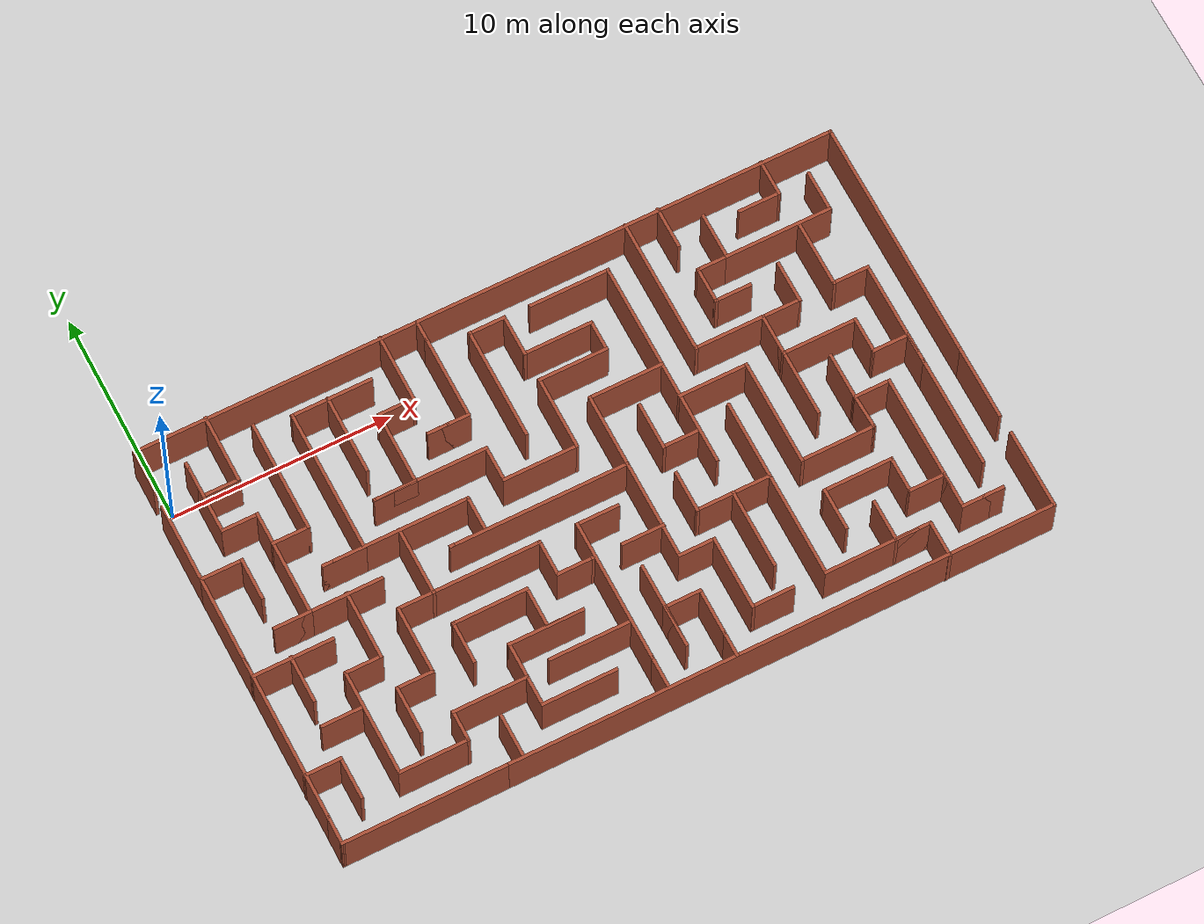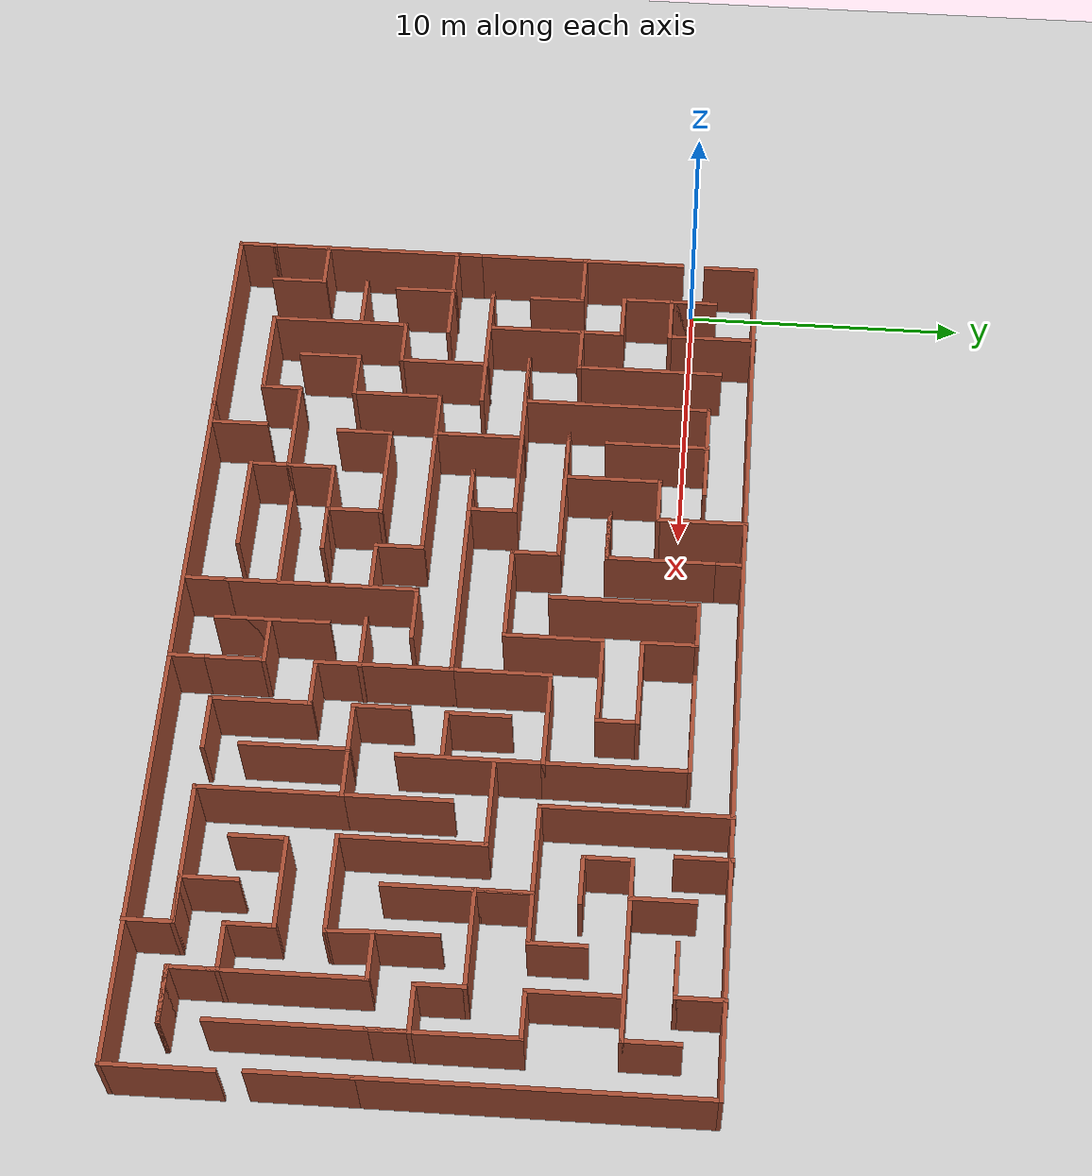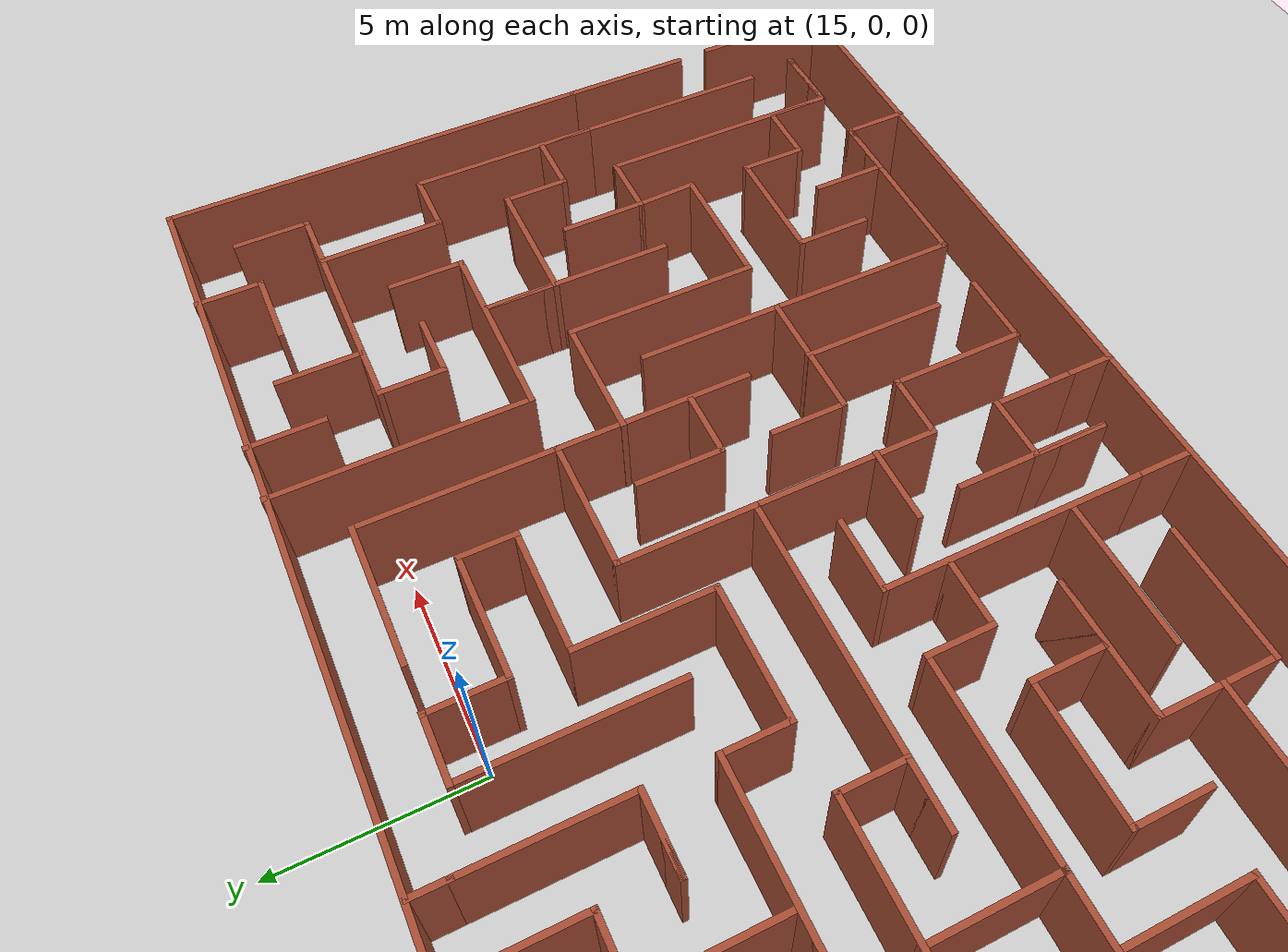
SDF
<sdf version="1.7">
 <world name="default">
  <light name="sun" type="directional">
   <pose>0 0 10 0 -0 0</pose>
   <diffuse>0.8 0.8 0.8 1</diffuse>
   <specular>0.2 0.2 0.2 1</specular>
   <attenuation>
    <range>1000</range>
    <constant>0.9</constant>
    <linear>0.01</linear>
    <quadratic>0.001</quadratic>
   </attenuation>
   <direction>-0.5 0.1 -0.9</direction>
   <spot><inner_angle>0</inner_angle><outer_angle>0</outer_angle><falloff>0</falloff></spot>
  </light>
  <model name="ground_plane">
   <static>1</static>
   <link name="link">
    <collision name="collision">
     <geometry><plane><normal>0 0 1</normal><size>100 100</size></plane></geometry>
     <surface>
      <contact><collide_bitmask>65535</collide_bitmask></contact>
      <friction><ode><mu>100</mu><mu2>50</mu2></ode></friction>
     </surface>
    </collision>
    <visual name="visual">
     <cast_shadows>0</cast_shadows>
     <geometry><plane><normal>0 0 1</normal><size>100 100</size></plane></geometry>
     <material>
      <script><uri>file://media/materials/scripts/gazebo.material</uri><name>Gazebo/Grey</name></script>
     </material>
    </visual>
   </link>
  </model>
  <gravity>0 0 -9.8</gravity>
  <magnetic_field>6e-06 2.3e-05 -4.2e-05</magnetic_field>
  <atmosphere type="adiabatic"/>
  <physics type="ode">
   <max_step_size>0.001</max_step_size>
   <real_time_factor>1</real_time_factor>
   <real_time_update_rate>1000</real_time_update_rate>
  </physics>
  <scene><ambient>0.4 0.4 0.4 1</ambient><background>0.7 0.7 0.7 1</background><shadows>1</shadows></scene>
  <audio><device>default</device></audio>
  <spherical_coordinates>
   <surface_model>EARTH_WGS84</surface_model>
   <latitude_deg>0</latitude_deg>
   <longitude_deg>0</longitude_deg>
   <elevation>0</elevation>
   <heading_deg>0</heading_deg>
  </spherical_coordinates>
  <model name="model_maze_2">
   <pose>15.6512 -7.28491 0 0 -0 0</pose>
   <link name="Wall_0">
    <collision name="Wall_0_Collision">
     <geometry><box><size>2 0.15 2.5</size></box></geometry>
     <pose>0 0 1.25 0 -0 0</pose>
    </collision>
    <visual name="Wall_0_Visual">
     <pose>0 0 1.25 0 -0 0</pose>
     <geometry><box><size>2 0.15 2.5</size></box></geometry>
     <material>
      <script><uri>file://media/materials/scripts/gazebo.material</uri><name>Gazebo/Bricks</name></script>
      <ambient>1 1 1 1</ambient>
     </material>
     <meta><layer>0</layer></meta>
    </visual>
    <pose>-16.1592 8.67968 0 0 -0 1.5708</pose>
   </link>
   <link name="Wall_1">
    <collision name="Wall_1_Collision">
     <geometry><box><size>32.5 0.15 2.5</size></box></geometry>
     <pose>0 0 1.25 0 -0 0</pose>
    </collision>
    <visual name="Wall_1_Visual">
     <pose>0 0 1.25 0 -0 0</pose>
     <geometry><box><size>32.5 0.15 2.5</size></box></geometry>
     <material>
      <script><uri>file://media/materials/scripts/gazebo.material</uri><name>Gazebo/Bricks</name></script>
      <ambient>1 1 1 1</ambient>
     </material>
     <meta><layer>0</layer></meta>
    </visual>
    <pose>0.01583 9.60468 0 0 -0 0</pose>
   </link>
   <link name="Wall_10">
    <collision name="Wall_10_Collision">
     <geometry><box><size>1.75 0.15 2.5</size></box></geometry>
     <pose>0 0 1.25 0 -0 0</pose>
    </collision>
    <visual name="Wall_10_Visual">
     <pose>0 0 1.25 0 -0 0</pose>
     <geometry><box><size>1.75 0.15 2.5</size></box></geometry>
     <material>
      <script><uri>file://media/materials/scripts/gazebo.material</uri><name>Gazebo/Bricks</name></script>
      <ambient>1 1 1 1</ambient>
     </material>
     <meta><layer>0</layer></meta>
    </visual>
    <pose>-13.6978 -0.048612 0 0 -0 3.14159</pose>
   </link>
   <link name="Wall_100">
    <collision name="Wall_100_Collision">
     <geometry><box><size>1.75 0.15 2.5</size></box></geometry>
     <pose>0 0 1.25 0 -0 0</pose>
    </collision>
    <visual name="Wall_100_Visual">
     <pose>0 0 1.25 0 -0 0</pose>
     <geometry><box><size>1.75 0.15 2.5</size></box></geometry>
     <material>
      <script><uri>file://media/materials/scripts/gazebo.material</uri><name>Gazebo/Bricks</name></script>
      <ambient>1 1 1 1</ambient>
     </material>
     <meta><layer>0</layer></meta>
    </visual>
    <pose>11.303 -5.61671 0 0 -0 1.5708</pose>
   </link>
   <link name="Wall_101">
    <collision name="Wall_101_Collision">
     <geometry><box><size>3.25 0.15 2.5</size></box></geometry>
     <pose>0 0 1.25 0 -0 0</pose>
    </collision>
    <visual name="Wall_101_Visual">
     <pose>0 0 1.25 0 -0 0</pose>
     <geometry><box><size>3.25 0.15 2.5</size></box></geometry>
     <material>
      <script><uri>file://media/materials/scripts/gazebo.material</uri><name>Gazebo/Bricks</name></script>
      <ambient>1 1 1 1</ambient>
     </material>
     <meta><layer>0</layer></meta>
    </visual>
    <pose>9.75296 -4.81671 0 0 -0 3.14159</pose>
   </link>
   <link name="Wall_102">
    <collision name="Wall_102_Collision">
     <geometry><box><size>2 0.15 2.5</size></box></geometry>
     <pose>0 0 1.25 0 -0 0</pose>
    </collision>
    <visual name="Wall_102_Visual">
     <pose>0 0 1.25 0 -0 0</pose>
     <geometry><box><size>2 0.15 2.5</size></box></geometry>
     <material>
      <script><uri>file://media/materials/scripts/gazebo.material</uri><name>Gazebo/Bricks</name></script>
      <ambient>1 1 1 1</ambient>
     </material>
     <meta><layer>0</layer></meta>
    </visual>
    <pose>8.20296 -5.74171 0 0 -0 -1.5708</pose>
   </link>
   <link name="Wall_104">
    <collision name="Wall_104_Collision">
     <geometry><box><size>5.25 0.15 2.5</size></box></geometry>
     <pose>0 0 1.25 0 -0 0</pose>
    </collision>
    <visual name="Wall_104_Visual">
     <pose>0 0 1.25 0 -0 0</pose>
     <geometry><box><size>5.25 0.15 2.5</size></box></geometry>
     <material>
      <script><uri>file://media/materials/scripts/gazebo.material</uri><name>Gazebo/Bricks</name></script>
      <ambient>1 1 1 1</ambient>
     </material>
     <meta><layer>0</layer></meta>
    </visual>
    <pose>14.587 -4.07531 0 0 -0 -1.5708</pose>
   </link>
   <link name="Wall_106">
    <collision name="Wall_106_Collision">
     <geometry><box><size>3.5 0.15 2.5</size></box></geometry>
     <pose>0 0 1.25 0 -0 0</pose>
    </collision>
    <visual name="Wall_106_Visual">
     <pose>0 0 1.25 0 -0 0</pose>
     <geometry><box><size>3.5 0.15 2.5</size></box></geometry>
     <material>
      <script><uri>file://media/materials/scripts/gazebo.material</uri><name>Gazebo/Bricks</name></script>
      <ambient>1 1 1 1</ambient>
     </material>
     <meta><layer>0</layer></meta>
    </visual>
    <pose>16.1908 -3.42032 0 0 -0 -1.5708</pose>
   </link>
   <link name="Wall_108">
    <collision name="Wall_108_Collision">
     <geometry><box><size>4.75 0.15 2.5</size></box></geometry>
     <pose>0 0 1.25 0 -0 0</pose>
    </collision>
    <visual name="Wall_108_Visual">
     <pose>0 0 1.25 0 -0 0</pose>
     <geometry><box><size>4.75 0.15 2.5</size></box></geometry>
     <material>
      <script><uri>file://media/materials/scripts/gazebo.material</uri><name>Gazebo/Bricks</name></script>
      <ambient>1 1 1 1</ambient>
     </material>
     <meta><layer>0</layer></meta>
    </visual>
    <pose>1.57577 -2.37523 0 0 -0 -1.5708</pose>
   </link>
   <link name="Wall_109">
    <collision name="Wall_109_Collision">
     <geometry><box><size>1.75 0.15 2.5</size></box></geometry>
     <pose>0 0 1.25 0 -0 0</pose>
    </collision>
    <visual name="Wall_109_Visual">
     <pose>0 0 1.25 0 -0 0</pose>
     <geometry><box><size>1.75 0.15 2.5</size></box></geometry>
     <material>
      <script><uri>file://media/materials/scripts/gazebo.material</uri><name>Gazebo/Bricks</name></script>
      <ambient>1 1 1 1</ambient>
     </material>
     <meta><layer>0</layer></meta>
    </visual>
    <pose>2.37577 -4.67523 0 0 -0 0</pose>
   </link>
   <link name="Wall_11">
    <collision name="Wall_11_Collision">
     <geometry><box><size>5 0.15 2.5</size></box></geometry>
     <pose>0 0 1.25 0 -0 0</pose>
    </collision>
    <visual name="Wall_11_Visual">
     <pose>0 0 1.25 0 -0 0</pose>
     <geometry><box><size>5 0.15 2.5</size></box></geometry>
     <material>
      <script><uri>file://media/materials/scripts/gazebo.material</uri><name>Gazebo/Bricks</name></script>
      <ambient>1 1 1 1</ambient>
     </material>
     <meta><layer>0</layer></meta>
    </visual>
    <pose>-12.0728 -0.048612 0 0 -0 0</pose>
   </link>
   <link name="Wall_110">
    <collision name="Wall_110_Collision">
     <geometry><box><size>3.5 0.15 2.5</size></box></geometry>
     <pose>0 0 1.25 0 -0 0</pose>
    </collision>
    <visual name="Wall_110_Visual">
     <pose>0 0 1.25 0 -0 0</pose>
     <geometry><box><size>3.5 0.15 2.5</size></box></geometry>
     <material>
      <script><uri>file://media/materials/scripts/gazebo.material</uri><name>Gazebo/Bricks</name></script>
      <ambient>1 1 1 1</ambient>
     </material>
     <meta><layer>0</layer></meta>
    </visual>
    <pose>3.17577 -6.35023 0 0 -0 -1.5708</pose>
   </link>
   <link name="Wall_111">
    <collision name="Wall_111_Collision">
     <geometry><box><size>2 0.15 2.5</size></box></geometry>
     <pose>0 0 1.25 0 -0 0</pose>
    </collision>
    <visual name="Wall_111_Visual">
     <pose>0 0 1.25 0 -0 0</pose>
     <geometry><box><size>2 0.15 2.5</size></box></geometry>
     <material>
      <script><uri>file://media/materials/scripts/gazebo.material</uri><name>Gazebo/Bricks</name></script>
      <ambient>1 1 1 1</ambient>
     </material>
     <meta><layer>0</layer></meta>
    </visual>
    <pose>4.10077 -8.02523 0 0 -0 0</pose>
   </link>
   <link name="Wall_113">
    <collision name="Wall_113_Collision">
     <geometry><box><size>3.75 0.15 2.5</size></box></geometry>
     <pose>0 0 1.25 0 -0 0</pose>
    </collision>
    <visual name="Wall_113_Visual">
     <pose>0 0 1.25 0 -0 0</pose>
     <geometry><box><size>3.75 0.15 2.5</size></box></geometry>
     <material>
      <script><uri>file://media/materials/scripts/gazebo.material</uri><name>Gazebo/Bricks</name></script>
      <ambient>1 1 1 1</ambient>
     </material>
     <meta><layer>0</layer></meta>
    </visual>
    <pose>6.51493 -1.41297 0 0 -0 -1.5708</pose>
   </link>
   <link name="Wall_114">
    <collision name="Wall_114_Collision">
     <geometry><box><size>3.5 0.15 2.5</size></box></geometry>
     <pose>0 0 1.25 0 -0 0</pose>
    </collision>
    <visual name="Wall_114_Visual">
     <pose>0 0 1.25 0 -0 0</pose>
     <geometry><box><size>3.5 0.15 2.5</size></box></geometry>
     <material>
      <script><uri>file://media/materials/scripts/gazebo.material</uri><name>Gazebo/Bricks</name></script>
      <ambient>1 1 1 1</ambient>
     </material>
     <meta><layer>0</layer></meta>
    </visual>
    <pose>4.83993 -3.21297 0 0 -0 3.14159</pose>
   </link>
   <link name="Wall_115">
    <collision name="Wall_115_Collision">
     <geometry><box><size>2 0.15 2.5</size></box></geometry>
     <pose>0 0 1.25 0 -0 0</pose>
    </collision>
    <visual name="Wall_115_Visual">
     <pose>0 0 1.25 0 -0 0</pose>
     <geometry><box><size>2 0.15 2.5</size></box></geometry>
     <material>
      <script><uri>file://media/materials/scripts/gazebo.material</uri><name>Gazebo/Bricks</name></script>
      <ambient>1 1 1 1</ambient>
     </material>
     <meta><layer>0</layer></meta>
    </visual>
    <pose>3.16493 -2.28797 0 0 -0 1.5708</pose>
   </link>
   <link name="Wall_117">
    <collision name="Wall_117_Collision">
     <geometry><box><size>5 0.15 2.5</size></box></geometry>
     <pose>0 0 1.25 0 -0 0</pose>
    </collision>
    <visual name="Wall_117_Visual">
     <pose>0 0 1.25 0 -0 0</pose>
     <geometry><box><size>5 0.15 2.5</size></box></geometry>
     <material>
      <script><uri>file://media/materials/scripts/gazebo.material</uri><name>Gazebo/Bricks</name></script>
      <ambient>1 1 1 1</ambient>
     </material>
     <meta><layer>0</layer></meta>
    </visual>
    <pose>6.51493 -5.63797 0 0 -0 -1.5708</pose>
   </link>
   <link name="Wall_118">
    <collision name="Wall_118_Collision">
     <geometry><box><size>5 0.15 2.5</size></box></geometry>
     <pose>0 0 1.25 0 -0 0</pose>
    </collision>
    <visual name="Wall_118_Visual">
     <pose>0 0 1.25 0 -0 0</pose>
     <geometry><box><size>5 0.15 2.5</size></box></geometry>
     <material>
      <script><uri>file://media/materials/scripts/gazebo.material</uri><name>Gazebo/Bricks</name></script>
      <ambient>1 1 1 1</ambient>
     </material>
     <meta><layer>0</layer></meta>
    </visual>
    <pose>8.93993 -8.06297 0 0 -0 0</pose>
   </link>
   <link name="Wall_119">
    <collision name="Wall_119_Collision">
     <geometry><box><size>1.75 0.15 2.5</size></box></geometry>
     <pose>0 0 1.25 0 -0 0</pose>
    </collision>
    <visual name="Wall_119_Visual">
     <pose>0 0 1.25 0 -0 0</pose>
     <geometry><box><size>1.75 0.15 2.5</size></box></geometry>
     <material>
      <script><uri>file://media/materials/scripts/gazebo.material</uri><name>Gazebo/Bricks</name></script>
      <ambient>1 1 1 1</ambient>
     </material>
     <meta><layer>0</layer></meta>
    </visual>
    <pose>10.5649 -8.06297 0 0 -0 3.14159</pose>
   </link>
   <link name="Wall_120">
    <collision name="Wall_120_Collision">
     <geometry><box><size>2 0.15 2.5</size></box></geometry>
     <pose>0 0 1.25 0 -0 0</pose>
    </collision>
    <visual name="Wall_120_Visual">
     <pose>0 0 1.25 0 -0 0</pose>
     <geometry><box><size>2 0.15 2.5</size></box></geometry>
     <material>
      <script><uri>file://media/materials/scripts/gazebo.material</uri><name>Gazebo/Bricks</name></script>
      <ambient>1 1 1 1</ambient>
     </material>
     <meta><layer>0</layer></meta>
    </visual>
    <pose>9.76493 -7.13797 0 0 -0 1.5708</pose>
   </link>
   <link name="Wall_122">
    <collision name="Wall_122_Collision">
     <geometry><box><size>3.75 0.15 2.5</size></box></geometry>
     <pose>0 0 1.25 0 -0 0</pose>
    </collision>
    <visual name="Wall_122_Visual">
     <pose>0 0 1.25 0 -0 0</pose>
     <geometry><box><size>3.75 0.15 2.5</size></box></geometry>
     <material>
      <script><uri>file://media/materials/scripts/gazebo.material</uri><name>Gazebo/Bricks</name></script>
      <ambient>1 1 1 1</ambient>
     </material>
     <meta><layer>0</layer></meta>
    </visual>
    <pose>4.82639 -4.99822 0 0 -0 -1.5708</pose>
   </link>
   <link name="Wall_124">
    <collision name="Wall_124_Collision">
     <geometry><box><size>2 0.15 2.5</size></box></geometry>
     <pose>0 0 1.25 0 -0 0</pose>
    </collision>
    <visual name="Wall_124_Visual">
     <pose>0 0 1.25 0 -0 0</pose>
     <geometry><box><size>2 0.15 2.5</size></box></geometry>
     <material>
      <script><uri>file://media/materials/scripts/gazebo.material</uri><name>Gazebo/Bricks</name></script>
      <ambient>1 1 1 1</ambient>
     </material>
     <meta><layer>0</layer></meta>
    </visual>
    <pose>0.686237 -3.17508 0 0 -0 3.14159</pose>
   </link>
   <link name="Wall_126">
    <collision name="Wall_126_Collision">
     <geometry><box><size>2 0.15 2.5</size></box></geometry>
     <pose>0 0 1.25 0 -0 0</pose>
    </collision>
    <visual name="Wall_126_Visual">
     <pose>0 0 1.25 0 -0 0</pose>
     <geometry><box><size>2 0.15 2.5</size></box></geometry>
     <material>
      <script><uri>file://media/materials/scripts/gazebo.material</uri><name>Gazebo/Bricks</name></script>
      <ambient>1 1 1 1</ambient>
     </material>
     <meta><layer>0</layer></meta>
    </visual>
    <pose>-0.562816 -1.55594 0 0 -0 3.14159</pose>
   </link>
   <link name="Wall_127">
    <collision name="Wall_127_Collision">
     <geometry><box><size>6.75 0.15 2.5</size></box></geometry>
     <pose>0 0 1.25 0 -0 0</pose>
    </collision>
    <visual name="Wall_127_Visual">
     <pose>0 0 1.25 0 -0 0</pose>
     <geometry><box><size>6.75 0.15 2.5</size></box></geometry>
     <material>
      <script><uri>file://media/materials/scripts/gazebo.material</uri><name>Gazebo/Bricks</name></script>
      <ambient>1 1 1 1</ambient>
     </material>
     <meta><layer>0</layer></meta>
    </visual>
    <pose>-1.48782 -4.85594 0 0 -0 -1.5708</pose>
   </link>
   <link name="Wall_13">
    <collision name="Wall_13_Collision">
     <geometry><box><size>3.75 0.15 2.5</size></box></geometry>
     <pose>0 0 1.25 0 -0 0</pose>
    </collision>
    <visual name="Wall_13_Visual">
     <pose>0 0 1.25 0 -0 0</pose>
     <geometry><box><size>3.75 0.15 2.5</size></box></geometry>
     <material>
      <script><uri>file://media/materials/scripts/gazebo.material</uri><name>Gazebo/Bricks</name></script>
      <ambient>1 1 1 1</ambient>
     </material>
     <meta><layer>0</layer></meta>
    </visual>
    <pose>-16.2054 5.05258 0 0 -0 -1.5708</pose>
   </link>
   <link name="Wall_130">
    <collision name="Wall_130_Collision">
     <geometry><box><size>1.75 0.15 2.5</size></box></geometry>
     <pose>0 0 1.25 0 -0 0</pose>
    </collision>
    <visual name="Wall_130_Visual">
     <pose>0 0 1.25 0 -0 0</pose>
     <geometry><box><size>1.75 0.15 2.5</size></box></geometry>
     <material>
      <script><uri>file://media/materials/scripts/gazebo.material</uri><name>Gazebo/Bricks</name></script>
      <ambient>1 1 1 1</ambient>
     </material>
     <meta><layer>0</layer></meta>
    </visual>
    <pose>-8.86181 -1.55587 0 0 -0 3.14159</pose>
   </link>
   <link name="Wall_131">
    <collision name="Wall_131_Collision">
     <geometry><box><size>3.25 0.15 2.5</size></box></geometry>
     <pose>0 0 1.25 0 -0 0</pose>
    </collision>
    <visual name="Wall_131_Visual">
     <pose>0 0 1.25 0 -0 0</pose>
     <geometry><box><size>3.25 0.15 2.5</size></box></geometry>
     <material>
      <script><uri>file://media/materials/scripts/gazebo.material</uri><name>Gazebo/Bricks</name></script>
      <ambient>1 1 1 1</ambient>
     </material>
     <meta><layer>0</layer></meta>
    </visual>
    <pose>-9.66181 -3.10587 0 0 -0 -1.5708</pose>
   </link>
   <link name="Wall_132">
    <collision name="Wall_132_Collision">
     <geometry><box><size>1.75 0.15 2.5</size></box></geometry>
     <pose>0 0 1.25 0 -0 0</pose>
    </collision>
    <visual name="Wall_132_Visual">
     <pose>0 0 1.25 0 -0 0</pose>
     <geometry><box><size>1.75 0.15 2.5</size></box></geometry>
     <material>
      <script><uri>file://media/materials/scripts/gazebo.material</uri><name>Gazebo/Bricks</name></script>
      <ambient>1 1 1 1</ambient>
     </material>
     <meta><layer>0</layer></meta>
    </visual>
    <pose>-10.4618 -4.65587 0 0 -0 3.14159</pose>
   </link>
   <link name="Wall_133">
    <collision name="Wall_133_Collision">
     <geometry><box><size>2.25 0.15 2.5</size></box></geometry>
     <pose>0 0 1.25 0 -0 0</pose>
    </collision>
    <visual name="Wall_133_Visual">
     <pose>0 0 1.25 0 -0 0</pose>
     <geometry><box><size>2.25 0.15 2.5</size></box></geometry>
     <material>
      <script><uri>file://media/materials/scripts/gazebo.material</uri><name>Gazebo/Bricks</name></script>
      <ambient>1 1 1 1</ambient>
     </material>
     <meta><layer>0</layer></meta>
    </visual>
    <pose>-11.2618 -5.70587 0 0 -0 -1.5708</pose>
   </link>
   <link name="Wall_135">
    <collision name="Wall_135_Collision">
     <geometry><box><size>5 0.15 2.5</size></box></geometry>
     <pose>0 0 1.25 0 -0 0</pose>
    </collision>
    <visual name="Wall_135_Visual">
     <pose>0 0 1.25 0 -0 0</pose>
     <geometry><box><size>5 0.15 2.5</size></box></geometry>
     <material>
      <script><uri>file://media/materials/scripts/gazebo.material</uri><name>Gazebo/Bricks</name></script>
      <ambient>1 1 1 1</ambient>
     </material>
     <meta><layer>0</layer></meta>
    </visual>
    <pose>-5.63681 -1.55587 0 0 -0 0</pose>
   </link>
   <link name="Wall_136">
    <collision name="Wall_136_Collision">
     <geometry><box><size>1.75 0.15 2.5</size></box></geometry>
     <pose>0 0 1.25 0 -0 0</pose>
    </collision>
    <visual name="Wall_136_Visual">
     <pose>0 0 1.25 0 -0 0</pose>
     <geometry><box><size>1.75 0.15 2.5</size></box></geometry>
     <material>
      <script><uri>file://media/materials/scripts/gazebo.material</uri><name>Gazebo/Bricks</name></script>
      <ambient>1 1 1 1</ambient>
     </material>
     <meta><layer>0</layer></meta>
    </visual>
    <pose>-3.21181 -2.35587 0 0 -0 -1.5708</pose>
   </link>
   <link name="Wall_137">
    <collision name="Wall_137_Collision">
     <geometry><box><size>1.75 0.15 2.5</size></box></geometry>
     <pose>0 0 1.25 0 -0 0</pose>
    </collision>
    <visual name="Wall_137_Visual">
     <pose>0 0 1.25 0 -0 0</pose>
     <geometry><box><size>1.75 0.15 2.5</size></box></geometry>
     <material>
      <script><uri>file://media/materials/scripts/gazebo.material</uri><name>Gazebo/Bricks</name></script>
      <ambient>1 1 1 1</ambient>
     </material>
     <meta><layer>0</layer></meta>
    </visual>
    <pose>-2.41181 -3.15587 0 0 -0 0</pose>
   </link>
   <link name="Wall_138">
    <collision name="Wall_138_Collision">
     <geometry><box><size>0.15 0.15 2.5</size></box></geometry>
     <pose>0 0 1.25 0 -0 0</pose>
    </collision>
    <visual name="Wall_138_Visual">
     <pose>0 0 1.25 0 -0 0</pose>
     <geometry><box><size>0.15 0.15 2.5</size></box></geometry>
     <material>
      <script><uri>file://media/materials/scripts/gazebo.material</uri><name>Gazebo/Bricks</name></script>
      <ambient>1 1 1 1</ambient>
     </material>
     <meta><layer>0</layer></meta>
    </visual>
    <pose>-1.61181 -3.15587 0 0 -0 0</pose>
   </link>
   <link name="Wall_14">
    <collision name="Wall_14_Collision">
     <geometry><box><size>2 0.15 2.5</size></box></geometry>
     <pose>0 0 1.25 0 -0 0</pose>
    </collision>
    <visual name="Wall_14_Visual">
     <pose>0 0 1.25 0 -0 0</pose>
     <geometry><box><size>2 0.15 2.5</size></box></geometry>
     <material>
      <script><uri>file://media/materials/scripts/gazebo.material</uri><name>Gazebo/Bricks</name></script>
      <ambient>1 1 1 1</ambient>
     </material>
     <meta><layer>0</layer></meta>
    </visual>
    <pose>-15.2804 3.25258 0 0 -0 0</pose>
   </link>
   <link name="Wall_140">
    <collision name="Wall_140_Collision">
     <geometry><box><size>3.25 0.15 2.5</size></box></geometry>
     <pose>0 0 1.25 0 -0 0</pose>
    </collision>
    <visual name="Wall_140_Visual">
     <pose>0 0 1.25 0 -0 0</pose>
     <geometry><box><size>3.25 0.15 2.5</size></box></geometry>
     <material>
      <script><uri>file://media/materials/scripts/gazebo.material</uri><name>Gazebo/Bricks</name></script>
      <ambient>1 1 1 1</ambient>
     </material>
     <meta><layer>0</layer></meta>
    </visual>
    <pose>-11.2176 -1.56101 0 0 -0 -1.5708</pose>
   </link>
   <link name="Wall_141">
    <collision name="Wall_141_Collision">
     <geometry><box><size>1.75 0.15 2.5</size></box></geometry>
     <pose>0 0 1.25 0 -0 0</pose>
    </collision>
    <visual name="Wall_141_Visual">
     <pose>0 0 1.25 0 -0 0</pose>
     <geometry><box><size>1.75 0.15 2.5</size></box></geometry>
     <material>
      <script><uri>file://media/materials/scripts/gazebo.material</uri><name>Gazebo/Bricks</name></script>
      <ambient>1 1 1 1</ambient>
     </material>
     <meta><layer>0</layer></meta>
    </visual>
    <pose>-12.0176 -3.11101 0 0 -0 3.14159</pose>
   </link>
   <link name="Wall_142">
    <collision name="Wall_142_Collision">
     <geometry><box><size>5 0.15 2.5</size></box></geometry>
     <pose>0 0 1.25 0 -0 0</pose>
    </collision>
    <visual name="Wall_142_Visual">
     <pose>0 0 1.25 0 -0 0</pose>
     <geometry><box><size>5 0.15 2.5</size></box></geometry>
     <material>
      <script><uri>file://media/materials/scripts/gazebo.material</uri><name>Gazebo/Bricks</name></script>
      <ambient>1 1 1 1</ambient>
     </material>
     <meta><layer>0</layer></meta>
    </visual>
    <pose>-12.8176 -5.53601 0 0 -0 -1.5708</pose>
   </link>
   <link name="Wall_143">
    <collision name="Wall_143_Collision">
     <geometry><box><size>3.25 0.15 2.5</size></box></geometry>
     <pose>0 0 1.25 0 -0 0</pose>
    </collision>
    <visual name="Wall_143_Visual">
     <pose>0 0 1.25 0 -0 0</pose>
     <geometry><box><size>3.25 0.15 2.5</size></box></geometry>
     <material>
      <script><uri>file://media/materials/scripts/gazebo.material</uri><name>Gazebo/Bricks</name></script>
      <ambient>1 1 1 1</ambient>
     </material>
     <meta><layer>0</layer></meta>
    </visual>
    <pose>-11.2676 -7.96101 0 0 -0 0</pose>
   </link>
   <link name="Wall_144">
    <collision name="Wall_144_Collision">
     <geometry><box><size>1.5 0.15 2.5</size></box></geometry>
     <pose>0 0 1.25 0 -0 0</pose>
    </collision>
    <visual name="Wall_144_Visual">
     <pose>0 0 1.25 0 -0 0</pose>
     <geometry><box><size>1.5 0.15 2.5</size></box></geometry>
     <material>
      <script><uri>file://media/materials/scripts/gazebo.material</uri><name>Gazebo/Bricks</name></script>
      <ambient>1 1 1 1</ambient>
     </material>
     <meta><layer>0</layer></meta>
    </visual>
    <pose>-9.71757 -7.28601 0 0 -0 1.5708</pose>
   </link>
   <link name="Wall_145">
    <collision name="Wall_145_Collision">
     <geometry><box><size>3.5 0.15 2.5</size></box></geometry>
     <pose>0 0 1.25 0 -0 0</pose>
    </collision>
    <visual name="Wall_145_Visual">
     <pose>0 0 1.25 0 -0 0</pose>
     <geometry><box><size>3.5 0.15 2.5</size></box></geometry>
     <material>
      <script><uri>file://media/materials/scripts/gazebo.material</uri><name>Gazebo/Bricks</name></script>
      <ambient>1 1 1 1</ambient>
     </material>
     <meta><layer>0</layer></meta>
    </visual>
    <pose>-8.04257 -6.61101 0 0 -0 0</pose>
   </link>
   <link name="Wall_146">
    <collision name="Wall_146_Collision">
     <geometry><box><size>1.75 0.15 2.5</size></box></geometry>
     <pose>0 0 1.25 0 -0 0</pose>
    </collision>
    <visual name="Wall_146_Visual">
     <pose>0 0 1.25 0 -0 0</pose>
     <geometry><box><size>1.75 0.15 2.5</size></box></geometry>
     <material>
      <script><uri>file://media/materials/scripts/gazebo.material</uri><name>Gazebo/Bricks</name></script>
      <ambient>1 1 1 1</ambient>
     </material>
     <meta><layer>0</layer></meta>
    </visual>
    <pose>-6.36757 -5.81101 0 0 -0 1.5708</pose>
   </link>
   <link name="Wall_147">
    <collision name="Wall_147_Collision">
     <geometry><box><size>3.5 0.15 2.5</size></box></geometry>
     <pose>0 0 1.25 0 -0 0</pose>
    </collision>
    <visual name="Wall_147_Visual">
     <pose>0 0 1.25 0 -0 0</pose>
     <geometry><box><size>3.5 0.15 2.5</size></box></geometry>
     <material>
      <script><uri>file://media/materials/scripts/gazebo.material</uri><name>Gazebo/Bricks</name></script>
      <ambient>1 1 1 1</ambient>
     </material>
     <meta><layer>0</layer></meta>
    </visual>
    <pose>-4.69257 -5.01101 0 0 -0 0</pose>
   </link>
   <link name="Wall_148">
    <collision name="Wall_148_Collision">
     <geometry><box><size>1.75 0.15 2.5</size></box></geometry>
     <pose>0 0 1.25 0 -0 0</pose>
    </collision>
    <visual name="Wall_148_Visual">
     <pose>0 0 1.25 0 -0 0</pose>
     <geometry><box><size>1.75 0.15 2.5</size></box></geometry>
     <material>
      <script><uri>file://media/materials/scripts/gazebo.material</uri><name>Gazebo/Bricks</name></script>
      <ambient>1 1 1 1</ambient>
     </material>
     <meta><layer>0</layer></meta>
    </visual>
    <pose>-3.81757 -5.01101 0 0 -0 3.14159</pose>
   </link>
   <link name="Wall_149">
    <collision name="Wall_149_Collision">
     <geometry><box><size>2 0.15 2.5</size></box></geometry>
     <pose>0 0 1.25 0 -0 0</pose>
    </collision>
    <visual name="Wall_149_Visual">
     <pose>0 0 1.25 0 -0 0</pose>
     <geometry><box><size>2 0.15 2.5</size></box></geometry>
     <material>
      <script><uri>file://media/materials/scripts/gazebo.material</uri><name>Gazebo/Bricks</name></script>
      <ambient>1 1 1 1</ambient>
     </material>
     <meta><layer>0</layer></meta>
    </visual>
    <pose>-4.61757 -4.08601 0 0 -0 1.5708</pose>
   </link>
   <link name="Wall_15">
    <collision name="Wall_15_Collision">
     <geometry><box><size>2 0.15 2.5</size></box></geometry>
     <pose>0 0 1.25 0 -0 0</pose>
    </collision>
    <visual name="Wall_15_Visual">
     <pose>0 0 1.25 0 -0 0</pose>
     <geometry><box><size>2 0.15 2.5</size></box></geometry>
     <material>
      <script><uri>file://media/materials/scripts/gazebo.material</uri><name>Gazebo/Bricks</name></script>
      <ambient>1 1 1 1</ambient>
     </material>
     <meta><layer>0</layer></meta>
    </visual>
    <pose>-14.3554 2.32758 0 0 -0 -1.5708</pose>
   </link>
   <link name="Wall_150">
    <collision name="Wall_150_Collision">
     <geometry><box><size>3.5 0.15 2.5</size></box></geometry>
     <pose>0 0 1.25 0 -0 0</pose>
    </collision>
    <visual name="Wall_150_Visual">
     <pose>0 0 1.25 0 -0 0</pose>
     <geometry><box><size>3.5 0.15 2.5</size></box></geometry>
     <material>
      <script><uri>file://media/materials/scripts/gazebo.material</uri><name>Gazebo/Bricks</name></script>
      <ambient>1 1 1 1</ambient>
     </material>
     <meta><layer>0</layer></meta>
    </visual>
    <pose>-6.29257 -3.16101 0 0 -0 3.14159</pose>
   </link>
   <link name="Wall_151">
    <collision name="Wall_151_Collision">
     <geometry><box><size>2 0.15 2.5</size></box></geometry>
     <pose>0 0 1.25 0 -0 0</pose>
    </collision>
    <visual name="Wall_151_Visual">
     <pose>0 0 1.25 0 -0 0</pose>
     <geometry><box><size>2 0.15 2.5</size></box></geometry>
     <material>
      <script><uri>file://media/materials/scripts/gazebo.material</uri><name>Gazebo/Bricks</name></script>
      <ambient>1 1 1 1</ambient>
     </material>
     <meta><layer>0</layer></meta>
    </visual>
    <pose>-7.96757 -4.08601 0 0 -0 -1.5708</pose>
   </link>
   <link name="Wall_153">
    <collision name="Wall_153_Collision">
     <geometry><box><size>3.75 0.15 2.5</size></box></geometry>
     <pose>0 0 1.25 0 -0 0</pose>
    </collision>
    <visual name="Wall_153_Visual">
     <pose>0 0 1.25 0 -0 0</pose>
     <geometry><box><size>3.75 0.15 2.5</size></box></geometry>
     <material>
      <script><uri>file://media/materials/scripts/gazebo.material</uri><name>Gazebo/Bricks</name></script>
      <ambient>1 1 1 1</ambient>
     </material>
     <meta><layer>0</layer></meta>
    </visual>
    <pose>-14.4054 -1.53763 0 0 -0 3.14159</pose>
   </link>
   <link name="Wall_154">
    <collision name="Wall_154_Collision">
     <geometry><box><size>0.15 0.15 2.5</size></box></geometry>
     <pose>0 0 1.25 0 -0 0</pose>
    </collision>
    <visual name="Wall_154_Visual">
     <pose>0 0 1.25 0 -0 0</pose>
     <geometry><box><size>0.15 0.15 2.5</size></box></geometry>
     <material>
      <script><uri>file://media/materials/scripts/gazebo.material</uri><name>Gazebo/Bricks</name></script>
      <ambient>1 1 1 1</ambient>
     </material>
     <meta><layer>0</layer></meta>
    </visual>
    <pose>-16.2054 -1.53763 0 0 -0 0</pose>
   </link>
   <link name="Wall_155">
    <collision name="Wall_155_Collision">
     <geometry><box><size>1 0.15 2.5</size></box></geometry>
     <pose>0 0 1.25 0 -0 0</pose>
    </collision>
    <visual name="Wall_155_Visual">
     <pose>0 0 1.25 0 -0 0</pose>
     <geometry><box><size>1 0.15 2.5</size></box></geometry>
     <material>
      <script><uri>file://media/materials/scripts/gazebo.material</uri><name>Gazebo/Bricks</name></script>
      <ambient>1 1 1 1</ambient>
     </material>
     <meta><layer>0</layer></meta>
    </visual>
    <pose>-16.2054 -1.11263 0 0 -0 1.5708</pose>
   </link>
   <link name="Wall_157">
    <collision name="Wall_157_Collision">
     <geometry><box><size>2.25 0.15 2.5</size></box></geometry>
     <pose>0 0 1.25 0 -0 0</pose>
    </collision>
    <visual name="Wall_157_Visual">
     <pose>0 0 1.25 0 -0 0</pose>
     <geometry><box><size>2.25 0.15 2.5</size></box></geometry>
     <material>
      <script><uri>file://media/materials/scripts/gazebo.material</uri><name>Gazebo/Bricks</name></script>
      <ambient>1 1 1 1</ambient>
     </material>
     <meta><layer>0</layer></meta>
    </visual>
    <pose>-14.479 -2.54137 0 0 -0 -1.5708</pose>
   </link>
   <link name="Wall_159">
    <collision name="Wall_159_Collision">
     <geometry><box><size>7 0.15 2.5</size></box></geometry>
     <pose>0 0 1.25 0 -0 0</pose>
    </collision>
    <visual name="Wall_159_Visual">
     <pose>0 0 1.25 0 -0 0</pose>
     <geometry><box><size>7 0.15 2.5</size></box></geometry>
     <material>
      <script><uri>file://media/materials/scripts/gazebo.material</uri><name>Gazebo/Bricks</name></script>
      <ambient>1 1 1 1</ambient>
     </material>
     <meta><layer>0</layer></meta>
    </visual>
    <pose>-16.2054 -4.96263 0 0 -0 -1.5708</pose>
   </link>
   <link name="Wall_161">
    <collision name="Wall_161_Collision">
     <geometry><box><size>2 0.15 2.5</size></box></geometry>
     <pose>0 0 1.25 0 -0 0</pose>
    </collision>
    <visual name="Wall_161_Visual">
     <pose>0 0 1.25 0 -0 0</pose>
     <geometry><box><size>2 0.15 2.5</size></box></geometry>
     <material>
      <script><uri>file://media/materials/scripts/gazebo.material</uri><name>Gazebo/Bricks</name></script>
      <ambient>1 1 1 1</ambient>
     </material>
     <meta><layer>0</layer></meta>
    </visual>
    <pose>-13.7617 -4.75279 0 0 -0 3.14159</pose>
   </link>
   <link name="Wall_163">
    <collision name="Wall_163_Collision">
     <geometry><box><size>1.75 0.15 2.5</size></box></geometry>
     <pose>0 0 1.25 0 -0 0</pose>
    </collision>
    <visual name="Wall_163_Visual">
     <pose>0 0 1.25 0 -0 0</pose>
     <geometry><box><size>1.75 0.15 2.5</size></box></geometry>
     <material>
      <script><uri>file://media/materials/scripts/gazebo.material</uri><name>Gazebo/Bricks</name></script>
      <ambient>1 1 1 1</ambient>
     </material>
     <meta><layer>0</layer></meta>
    </visual>
    <pose>-15.4369 -6.3488 0 0 -0 0</pose>
   </link>
   <link name="Wall_164">
    <collision name="Wall_164_Collision">
     <geometry><box><size>2 0.15 2.5</size></box></geometry>
     <pose>0 0 1.25 0 -0 0</pose>
    </collision>
    <visual name="Wall_164_Visual">
     <pose>0 0 1.25 0 -0 0</pose>
     <geometry><box><size>2 0.15 2.5</size></box></geometry>
     <material>
      <script><uri>file://media/materials/scripts/gazebo.material</uri><name>Gazebo/Bricks</name></script>
      <ambient>1 1 1 1</ambient>
     </material>
     <meta><layer>0</layer></meta>
    </visual>
    <pose>-14.6369 -7.2738 0 0 -0 -1.5708</pose>
   </link>
   <link name="Wall_166">
    <collision name="Wall_166_Collision">
     <geometry><box><size>5 0.15 2.5</size></box></geometry>
     <pose>0 0 1.25 0 -0 0</pose>
    </collision>
    <visual name="Wall_166_Visual">
     <pose>0 0 1.25 0 -0 0</pose>
     <geometry><box><size>5 0.15 2.5</size></box></geometry>
     <material>
      <script><uri>file://media/materials/scripts/gazebo.material</uri><name>Gazebo/Bricks</name></script>
      <ambient>1 1 1 1</ambient>
     </material>
     <meta><layer>0</layer></meta>
    </visual>
    <pose>8.01446 -0.76522 0 0 -0 -1.5708</pose>
   </link>
   <link name="Wall_167">
    <collision name="Wall_167_Collision">
     <geometry><box><size>3.5 0.15 2.5</size></box></geometry>
     <pose>0 0 1.25 0 -0 0</pose>
    </collision>
    <visual name="Wall_167_Visual">
     <pose>0 0 1.25 0 -0 0</pose>
     <geometry><box><size>3.5 0.15 2.5</size></box></geometry>
     <material>
      <script><uri>file://media/materials/scripts/gazebo.material</uri><name>Gazebo/Bricks</name></script>
      <ambient>1 1 1 1</ambient>
     </material>
     <meta><layer>0</layer></meta>
    </visual>
    <pose>9.68946 -3.19022 0 0 -0 0</pose>
   </link>
   <link name="Wall_168">
    <collision name="Wall_168_Collision">
     <geometry><box><size>1.67475 0.15 2.5</size></box></geometry>
     <pose>0 0 1.25 0 -0 0</pose>
    </collision>
    <visual name="Wall_168_Visual">
     <pose>0 0 1.25 0 -0 0</pose>
     <geometry><box><size>1.67475 0.15 2.5</size></box></geometry>
     <material>
      <script><uri>file://media/materials/scripts/gazebo.material</uri><name>Gazebo/Bricks</name></script>
      <ambient>1 1 1 1</ambient>
     </material>
     <meta><layer>0</layer></meta>
    </visual>
    <pose>11.3337 -2.42847 0 0 -0 1.61114</pose>
   </link>
   <link name="Wall_17">
    <collision name="Wall_17_Collision">
     <geometry><box><size>4.75 0.15 2.5</size></box></geometry>
     <pose>0 0 1.25 0 -0 0</pose>
    </collision>
    <visual name="Wall_17_Visual">
     <pose>0 0 1.25 0 -0 0</pose>
     <geometry><box><size>4.75 0.15 2.5</size></box></geometry>
     <material>
      <script><uri>file://media/materials/scripts/gazebo.material</uri><name>Gazebo/Bricks</name></script>
      <ambient>1 1 1 1</ambient>
     </material>
     <meta><layer>0</layer></meta>
    </visual>
    <pose>-16.2054 0.952584 0 0 -0 -1.5708</pose>
   </link>
   <link name="Wall_170">
    <collision name="Wall_170_Collision">
     <geometry><box><size>3.75 0.15 2.5</size></box></geometry>
     <pose>0 0 1.25 0 -0 0</pose>
    </collision>
    <visual name="Wall_170_Visual">
     <pose>0 0 1.25 0 -0 0</pose>
     <geometry><box><size>3.75 0.15 2.5</size></box></geometry>
     <material>
      <script><uri>file://media/materials/scripts/gazebo.material</uri><name>Gazebo/Bricks</name></script>
      <ambient>1 1 1 1</ambient>
     </material>
     <meta><layer>0</layer></meta>
    </visual>
    <pose>-3.40204 -6.3451 0 0 -0 0</pose>
   </link>
   <link name="Wall_172">
    <collision name="Wall_172_Collision">
     <geometry><box><size>4 0.15 2.5</size></box></geometry>
     <pose>0 0 1.25 0 -0 0</pose>
    </collision>
    <visual name="Wall_172_Visual">
     <pose>0 0 1.25 0 -0 0</pose>
     <geometry><box><size>4 0.15 2.5</size></box></geometry>
     <material>
      <script><uri>file://media/materials/scripts/gazebo.material</uri><name>Gazebo/Bricks</name></script>
      <ambient>1 1 1 1</ambient>
     </material>
     <meta><layer>0</layer></meta>
    </visual>
    <pose>0.008124 -6.36179 0 0 -0 -1.5708</pose>
   </link>
   <link name="Wall_173">
    <collision name="Wall_173_Collision">
     <geometry><box><size>2 0.15 2.5</size></box></geometry>
     <pose>0 0 1.25 0 -0 0</pose>
    </collision>
    <visual name="Wall_173_Visual">
     <pose>0 0 1.25 0 -0 0</pose>
     <geometry><box><size>2 0.15 2.5</size></box></geometry>
     <material>
      <script><uri>file://media/materials/scripts/gazebo.material</uri><name>Gazebo/Bricks</name></script>
      <ambient>1 1 1 1</ambient>
     </material>
     <meta><layer>0</layer></meta>
    </visual>
    <pose>0.008124 -7.36179 0 0 -0 1.5708</pose>
   </link>
   <link name="Wall_174">
    <collision name="Wall_174_Collision">
     <geometry><box><size>1.75 0.15 2.5</size></box></geometry>
     <pose>0 0 1.25 0 -0 0</pose>
    </collision>
    <visual name="Wall_174_Visual">
     <pose>0 0 1.25 0 -0 0</pose>
     <geometry><box><size>1.75 0.15 2.5</size></box></geometry>
     <material>
      <script><uri>file://media/materials/scripts/gazebo.material</uri><name>Gazebo/Bricks</name></script>
      <ambient>1 1 1 1</ambient>
     </material>
     <meta><layer>0</layer></meta>
    </visual>
    <pose>0.808124 -6.43679 0 0 -0 0</pose>
   </link>
   <link name="Wall_175">
    <collision name="Wall_175_Collision">
     <geometry><box><size>2.25 0.15 2.5</size></box></geometry>
     <pose>0 0 1.25 0 -0 0</pose>
    </collision>
    <visual name="Wall_175_Visual">
     <pose>0 0 1.25 0 -0 0</pose>
     <geometry><box><size>2.25 0.15 2.5</size></box></geometry>
     <material>
      <script><uri>file://media/materials/scripts/gazebo.material</uri><name>Gazebo/Bricks</name></script>
      <ambient>1 1 1 1</ambient>
     </material>
     <meta><layer>0</layer></meta>
    </visual>
    <pose>1.60812 -7.48679 0 0 -0 -1.5708</pose>
   </link>
   <link name="Wall_178">
    <collision name="Wall_178_Collision">
     <geometry><box><size>3.75 0.15 2.5</size></box></geometry>
     <pose>0 0 1.25 0 -0 0</pose>
    </collision>
    <visual name="Wall_178_Visual">
     <pose>0 0 1.25 0 -0 0</pose>
     <geometry><box><size>3.75 0.15 2.5</size></box></geometry>
     <material>
      <script><uri>file://media/materials/scripts/gazebo.material</uri><name>Gazebo/Bricks</name></script>
      <ambient>1 1 1 1</ambient>
     </material>
     <meta><layer>0</layer></meta>
    </visual>
    <pose>16.2369 -7.84031 0 0 -0 -1.5708</pose>
   </link>
   <link name="Wall_179">
    <collision name="Wall_179_Collision">
     <geometry><box><size>25.25 0.15 2.5</size></box></geometry>
     <pose>0 0 1.25 0 -0 0</pose>
    </collision>
    <visual name="Wall_179_Visual">
     <pose>0 0 1.25 0 -0 0</pose>
     <geometry><box><size>25.25 0.15 2.5</size></box></geometry>
     <material>
      <script><uri>file://media/materials/scripts/gazebo.material</uri><name>Gazebo/Bricks</name></script>
      <ambient>1 1 1 1</ambient>
     </material>
     <meta><layer>0</layer></meta>
    </visual>
    <pose>3.68691 -9.64031 0 0 -0 3.14159</pose>
   </link>
   <link name="Wall_181">
    <collision name="Wall_181_Collision">
     <geometry><box><size>1.5 0.15 2.5</size></box></geometry>
     <pose>0 0 1.25 0 -0 0</pose>
    </collision>
    <visual name="Wall_181_Visual">
     <pose>0 0 1.25 0 -0 0</pose>
     <geometry><box><size>1.5 0.15 2.5</size></box></geometry>
     <material>
      <script><uri>file://media/materials/scripts/gazebo.material</uri><name>Gazebo/Bricks</name></script>
      <ambient>1 1 1 1</ambient>
     </material>
     <meta><layer>0</layer></meta>
    </visual>
    <pose>-1.48782 -8.83094 0 0 -0 -1.5708</pose>
   </link>
   <link name="Wall_183">
    <collision name="Wall_183_Collision">
     <geometry><box><size>1.25 0.15 2.5</size></box></geometry>
     <pose>0 0 1.25 0 -0 0</pose>
    </collision>
    <visual name="Wall_183_Visual">
     <pose>0 0 1.25 0 -0 0</pose>
     <geometry><box><size>1.25 0.15 2.5</size></box></geometry>
     <material>
      <script><uri>file://media/materials/scripts/gazebo.material</uri><name>Gazebo/Bricks</name></script>
      <ambient>1 1 1 1</ambient>
     </material>
     <meta><layer>0</layer></meta>
    </visual>
    <pose>1.60812 -9.08679 0 0 -0 -1.5708</pose>
   </link>
   <link name="Wall_185">
    <collision name="Wall_185_Collision">
     <geometry><box><size>1.75 0.15 2.5</size></box></geometry>
     <pose>0 0 1.25 0 -0 0</pose>
    </collision>
    <visual name="Wall_185_Visual">
     <pose>0 0 1.25 0 -0 0</pose>
     <geometry><box><size>1.75 0.15 2.5</size></box></geometry>
     <material>
      <script><uri>file://media/materials/scripts/gazebo.material</uri><name>Gazebo/Bricks</name></script>
      <ambient>1 1 1 1</ambient>
     </material>
     <meta><layer>0</layer></meta>
    </visual>
    <pose>11.3649 -8.86297 0 0 -0 -1.5708</pose>
   </link>
   <link name="Wall_187">
    <collision name="Wall_187_Collision">
     <geometry><box><size>1.5 0.15 2.5</size></box></geometry>
     <pose>0 0 1.25 0 -0 0</pose>
    </collision>
    <visual name="Wall_187_Visual">
     <pose>0 0 1.25 0 -0 0</pose>
     <geometry><box><size>1.5 0.15 2.5</size></box></geometry>
     <material>
      <script><uri>file://media/materials/scripts/gazebo.material</uri><name>Gazebo/Bricks</name></script>
      <ambient>1 1 1 1</ambient>
     </material>
     <meta><layer>0</layer></meta>
    </visual>
    <pose>-6.36757 -7.28601 0 0 -0 -1.5708</pose>
   </link>
   <link name="Wall_188">
    <collision name="Wall_188_Collision">
     <geometry><box><size>3.5 0.15 2.5</size></box></geometry>
     <pose>0 0 1.25 0 -0 0</pose>
    </collision>
    <visual name="Wall_188_Visual">
     <pose>0 0 1.25 0 -0 0</pose>
     <geometry><box><size>3.5 0.15 2.5</size></box></geometry>
     <material>
      <script><uri>file://media/materials/scripts/gazebo.material</uri><name>Gazebo/Bricks</name></script>
      <ambient>1 1 1 1</ambient>
     </material>
     <meta><layer>0</layer></meta>
    </visual>
    <pose>-4.69257 -7.96101 0 0 -0 0</pose>
   </link>
   <link name="Wall_19">
    <collision name="Wall_19_Collision">
     <geometry><box><size>5.25 0.15 2.5</size></box></geometry>
     <pose>0 0 1.25 0 -0 0</pose>
    </collision>
    <visual name="Wall_19_Visual">
     <pose>0 0 1.25 0 -0 0</pose>
     <geometry><box><size>5.25 0.15 2.5</size></box></geometry>
     <material>
      <script><uri>file://media/materials/scripts/gazebo.material</uri><name>Gazebo/Bricks</name></script>
      <ambient>1 1 1 1</ambient>
     </material>
     <meta><layer>0</layer></meta>
    </visual>
    <pose>-11.3017 5.8986 0 0 -0 -1.5708</pose>
   </link>
   <link name="Wall_190">
    <collision name="Wall_190_Collision">
     <geometry><box><size>2 0.15 2.5</size></box></geometry>
     <pose>0 0 1.25 0 -0 0</pose>
    </collision>
    <visual name="Wall_190_Visual">
     <pose>0 0 1.25 0 -0 0</pose>
     <geometry><box><size>2 0.15 2.5</size></box></geometry>
     <material>
      <script><uri>file://media/materials/scripts/gazebo.material</uri><name>Gazebo/Bricks</name></script>
      <ambient>1 1 1 1</ambient>
     </material>
     <meta><layer>0</layer></meta>
    </visual>
    <pose>-8.06834 -8.56956 0 0 -0 -1.5708</pose>
   </link>
   <link name="Wall_192">
    <collision name="Wall_192_Collision">
     <geometry><box><size>7.5 0.15 2.5</size></box></geometry>
     <pose>0 0 1.25 0 -0 0</pose>
    </collision>
    <visual name="Wall_192_Visual">
     <pose>0 0 1.25 0 -0 0</pose>
     <geometry><box><size>7.5 0.15 2.5</size></box></geometry>
     <material>
      <script><uri>file://media/materials/scripts/gazebo.material</uri><name>Gazebo/Bricks</name></script>
      <ambient>1 1 1 1</ambient>
     </material>
     <meta><layer>0</layer></meta>
    </visual>
    <pose>-12.5381 -9.64031 0 0 -0 3.14159</pose>
   </link>
   <link name="Wall_193">
    <collision name="Wall_193_Collision">
     <geometry><box><size>1.40271 0.15 2.5</size></box></geometry>
     <pose>0 0 1.25 0 -0 0</pose>
    </collision>
    <visual name="Wall_193_Visual">
     <pose>0 0 1.25 0 -0 0</pose>
     <geometry><box><size>1.40271 0.15 2.5</size></box></geometry>
     <material>
      <script><uri>file://media/materials/scripts/gazebo.material</uri><name>Gazebo/Bricks</name></script>
      <ambient>1 1 1 1</ambient>
     </material>
     <meta><layer>0</layer></meta>
    </visual>
    <pose>-16.2092 -9.01397 0 0 -0 1.56466</pose>
   </link>
   <link name="Wall_2">
    <collision name="Wall_2_Collision">
     <geometry><box><size>11.5 0.15 2.5</size></box></geometry>
     <pose>0 0 1.25 0 -0 0</pose>
    </collision>
    <visual name="Wall_2_Visual">
     <pose>0 0 1.25 0 -0 0</pose>
     <geometry><box><size>11.5 0.15 2.5</size></box></geometry>
     <material>
      <script><uri>file://media/materials/scripts/gazebo.material</uri><name>Gazebo/Bricks</name></script>
      <ambient>1 1 1 1</ambient>
     </material>
     <meta><layer>0</layer></meta>
    </visual>
    <pose>16.1908 3.92968 0 0 -0 -1.5708</pose>
   </link>
   <link name="Wall_20">
    <collision name="Wall_20_Collision">
     <geometry><box><size>1.75 0.15 2.5</size></box></geometry>
     <pose>0 0 1.25 0 -0 0</pose>
    </collision>
    <visual name="Wall_20_Visual">
     <pose>0 0 1.25 0 -0 0</pose>
     <geometry><box><size>1.75 0.15 2.5</size></box></geometry>
     <material>
      <script><uri>file://media/materials/scripts/gazebo.material</uri><name>Gazebo/Bricks</name></script>
      <ambient>1 1 1 1</ambient>
     </material>
     <meta><layer>0</layer></meta>
    </visual>
    <pose>-12.1017 3.3486 0 0 -0 3.14159</pose>
   </link>
   <link name="Wall_22">
    <collision name="Wall_22_Collision">
     <geometry><box><size>3.75 0.15 2.5</size></box></geometry>
     <pose>0 0 1.25 0 -0 0</pose>
    </collision>
    <visual name="Wall_22_Visual">
     <pose>0 0 1.25 0 -0 0</pose>
     <geometry><box><size>3.75 0.15 2.5</size></box></geometry>
     <material>
      <script><uri>file://media/materials/scripts/gazebo.material</uri><name>Gazebo/Bricks</name></script>
      <ambient>1 1 1 1</ambient>
     </material>
     <meta><layer>0</layer></meta>
    </visual>
    <pose>-7.87423 8.12477 0 0 -0 3.14159</pose>
   </link>
   <link name="Wall_23">
    <collision name="Wall_23_Collision">
     <geometry><box><size>6.75 0.15 2.5</size></box></geometry>
     <pose>0 0 1.25 0 -0 0</pose>
    </collision>
    <visual name="Wall_23_Visual">
     <pose>0 0 1.25 0 -0 0</pose>
     <geometry><box><size>6.75 0.15 2.5</size></box></geometry>
     <material>
      <script><uri>file://media/materials/scripts/gazebo.material</uri><name>Gazebo/Bricks</name></script>
      <ambient>1 1 1 1</ambient>
     </material>
     <meta><layer>0</layer></meta>
    </visual>
    <pose>-9.67423 4.82477 0 0 -0 -1.5708</pose>
   </link>
   <link name="Wall_24">
    <collision name="Wall_24_Collision">
     <geometry><box><size>2 0.15 2.5</size></box></geometry>
     <pose>0 0 1.25 0 -0 0</pose>
    </collision>
    <visual name="Wall_24_Visual">
     <pose>0 0 1.25 0 -0 0</pose>
     <geometry><box><size>2 0.15 2.5</size></box></geometry>
     <material>
      <script><uri>file://media/materials/scripts/gazebo.material</uri><name>Gazebo/Bricks</name></script>
      <ambient>1 1 1 1</ambient>
     </material>
     <meta><layer>0</layer></meta>
    </visual>
    <pose>-10.5992 1.52477 0 0 -0 3.14159</pose>
   </link>
   <link name="Wall_25">
    <collision name="Wall_25_Collision">
     <geometry><box><size>6.75 0.15 2.5</size></box></geometry>
     <pose>0 0 1.25 0 -0 0</pose>
    </collision>
    <visual name="Wall_25_Visual">
     <pose>0 0 1.25 0 -0 0</pose>
     <geometry><box><size>6.75 0.15 2.5</size></box></geometry>
     <material>
      <script><uri>file://media/materials/scripts/gazebo.material</uri><name>Gazebo/Bricks</name></script>
      <ambient>1 1 1 1</ambient>
     </material>
     <meta><layer>0</layer></meta>
    </visual>
    <pose>-8.22423 1.52477 0 0 -0 0</pose>
   </link>
   <link name="Wall_26">
    <collision name="Wall_26_Collision">
     <geometry><box><size>1.75 0.15 2.5</size></box></geometry>
     <pose>0 0 1.25 0 -0 0</pose>
    </collision>
    <visual name="Wall_26_Visual">
     <pose>0 0 1.25 0 -0 0</pose>
     <geometry><box><size>1.75 0.15 2.5</size></box></geometry>
     <material>
      <script><uri>file://media/materials/scripts/gazebo.material</uri><name>Gazebo/Bricks</name></script>
      <ambient>1 1 1 1</ambient>
     </material>
     <meta><layer>0</layer></meta>
    </visual>
    <pose>-4.92422 0.724768 0 0 -0 -1.5708</pose>
   </link>
   <link name="Wall_27">
    <collision name="Wall_27_Collision">
     <geometry><box><size>1.75 0.15 2.5</size></box></geometry>
     <pose>0 0 1.25 0 -0 0</pose>
    </collision>
    <visual name="Wall_27_Visual">
     <pose>0 0 1.25 0 -0 0</pose>
     <geometry><box><size>1.75 0.15 2.5</size></box></geometry>
     <material>
      <script><uri>file://media/materials/scripts/gazebo.material</uri><name>Gazebo/Bricks</name></script>
      <ambient>1 1 1 1</ambient>
     </material>
     <meta><layer>0</layer></meta>
    </visual>
    <pose>-5.72423 -0.075232 0 0 -0 3.14159</pose>
   </link>
   <link name="Wall_28">
    <collision name="Wall_28_Collision">
     <geometry><box><size>8.25 0.15 2.5</size></box></geometry>
     <pose>0 0 1.25 0 -0 0</pose>
    </collision>
    <visual name="Wall_28_Visual">
     <pose>0 0 1.25 0 -0 0</pose>
     <geometry><box><size>8.25 0.15 2.5</size></box></geometry>
     <material>
      <script><uri>file://media/materials/scripts/gazebo.material</uri><name>Gazebo/Bricks</name></script>
      <ambient>1 1 1 1</ambient>
     </material>
     <meta><layer>0</layer></meta>
    </visual>
    <pose>-2.47423 -0.075232 0 0 -0 0</pose>
   </link>
   <link name="Wall_29">
    <collision name="Wall_29_Collision">
     <geometry><box><size>3.5 0.15 2.5</size></box></geometry>
     <pose>0 0 1.25 0 -0 0</pose>
    </collision>
    <visual name="Wall_29_Visual">
     <pose>0 0 1.25 0 -0 0</pose>
     <geometry><box><size>3.5 0.15 2.5</size></box></geometry>
     <material>
      <script><uri>file://media/materials/scripts/gazebo.material</uri><name>Gazebo/Bricks</name></script>
      <ambient>1 1 1 1</ambient>
     </material>
     <meta><layer>0</layer></meta>
    </visual>
    <pose>1.57577 1.59977 0 0 -0 1.5708</pose>
   </link>
   <link name="Wall_30">
    <collision name="Wall_30_Collision">
     <geometry><box><size>3.5 0.15 2.5</size></box></geometry>
     <pose>0 0 1.25 0 -0 0</pose>
    </collision>
    <visual name="Wall_30_Visual">
     <pose>0 0 1.25 0 -0 0</pose>
     <geometry><box><size>3.5 0.15 2.5</size></box></geometry>
     <material>
      <script><uri>file://media/materials/scripts/gazebo.material</uri><name>Gazebo/Bricks</name></script>
      <ambient>1 1 1 1</ambient>
     </material>
     <meta><layer>0</layer></meta>
    </visual>
    <pose>3.25077 3.27477 0 0 -0 0</pose>
   </link>
   <link name="Wall_31">
    <collision name="Wall_31_Collision">
     <geometry><box><size>5 0.15 2.5</size></box></geometry>
     <pose>0 0 1.25 0 -0 0</pose>
    </collision>
    <visual name="Wall_31_Visual">
     <pose>0 0 1.25 0 -0 0</pose>
     <geometry><box><size>5 0.15 2.5</size></box></geometry>
     <material>
      <script><uri>file://media/materials/scripts/gazebo.material</uri><name>Gazebo/Bricks</name></script>
      <ambient>1 1 1 1</ambient>
     </material>
     <meta><layer>0</layer></meta>
    </visual>
    <pose>4.92577 5.69977 0 0 -0 1.5708</pose>
   </link>
   <link name="Wall_32">
    <collision name="Wall_32_Collision">
     <geometry><box><size>3.75 0.15 2.5</size></box></geometry>
     <pose>0 0 1.25 0 -0 0</pose>
    </collision>
    <visual name="Wall_32_Visual">
     <pose>0 0 1.25 0 -0 0</pose>
     <geometry><box><size>3.75 0.15 2.5</size></box></geometry>
     <material>
      <script><uri>file://media/materials/scripts/gazebo.material</uri><name>Gazebo/Bricks</name></script>
      <ambient>1 1 1 1</ambient>
     </material>
     <meta><layer>0</layer></meta>
    </visual>
    <pose>3.12577 8.12477 0 0 -0 3.14159</pose>
   </link>
   <link name="Wall_34">
    <collision name="Wall_34_Collision">
     <geometry><box><size>2 0.15 2.5</size></box></geometry>
     <pose>0 0 1.25 0 -0 0</pose>
    </collision>
    <visual name="Wall_34_Visual">
     <pose>0 0 1.25 0 -0 0</pose>
     <geometry><box><size>2 0.15 2.5</size></box></geometry>
     <material>
      <script><uri>file://media/materials/scripts/gazebo.material</uri><name>Gazebo/Bricks</name></script>
      <ambient>1 1 1 1</ambient>
     </material>
     <meta><layer>0</layer></meta>
    </visual>
    <pose>-4.13103 4.86335 0 0 -0 3.14159</pose>
   </link>
   <link name="Wall_35">
    <collision name="Wall_35_Collision">
     <geometry><box><size>2 0.15 2.5</size></box></geometry>
     <pose>0 0 1.25 0 -0 0</pose>
    </collision>
    <visual name="Wall_35_Visual">
     <pose>0 0 1.25 0 -0 0</pose>
     <geometry><box><size>2 0.15 2.5</size></box></geometry>
     <material>
      <script><uri>file://media/materials/scripts/gazebo.material</uri><name>Gazebo/Bricks</name></script>
      <ambient>1 1 1 1</ambient>
     </material>
     <meta><layer>0</layer></meta>
    </visual>
    <pose>-4.13103 4.86335 0 0 -0 0</pose>
   </link>
   <link name="Wall_36">
    <collision name="Wall_36_Collision">
     <geometry><box><size>4 0.15 2.5</size></box></geometry>
     <pose>0 0 1.25 0 -0 0</pose>
    </collision>
    <visual name="Wall_36_Visual">
     <pose>0 0 1.25 0 -0 0</pose>
     <geometry><box><size>4 0.15 2.5</size></box></geometry>
     <material>
      <script><uri>file://media/materials/scripts/gazebo.material</uri><name>Gazebo/Bricks</name></script>
      <ambient>1 1 1 1</ambient>
     </material>
     <meta><layer>0</layer></meta>
    </visual>
    <pose>-3.20603 6.78835 0 0 -0 1.5708</pose>
   </link>
   <link name="Wall_38">
    <collision name="Wall_38_Collision">
     <geometry><box><size>1 0.15 2.5</size></box></geometry>
     <pose>0 0 1.25 0 -0 0</pose>
    </collision>
    <visual name="Wall_38_Visual">
     <pose>0 0 1.25 0 -0 0</pose>
     <geometry><box><size>1 0.15 2.5</size></box></geometry>
     <material>
      <script><uri>file://media/materials/scripts/gazebo.material</uri><name>Gazebo/Bricks</name></script>
      <ambient>1 1 1 1</ambient>
     </material>
     <meta><layer>0</layer></meta>
    </visual>
    <pose>-3.20603 9.13835 0 0 -0 1.5708</pose>
   </link>
   <link name="Wall_4">
    <collision name="Wall_4_Collision">
     <geometry><box><size>3.25 0.15 2.5</size></box></geometry>
     <pose>0 0 1.25 0 -0 0</pose>
    </collision>
    <visual name="Wall_4_Visual">
     <pose>0 0 1.25 0 -0 0</pose>
     <geometry><box><size>3.25 0.15 2.5</size></box></geometry>
     <material>
      <script><uri>file://media/materials/scripts/gazebo.material</uri><name>Gazebo/Bricks</name></script>
      <ambient>1 1 1 1</ambient>
     </material>
     <meta><layer>0</layer></meta>
    </visual>
    <pose>-12.8978 8.10139 0 0 -0 -1.5708</pose>
   </link>
   <link name="Wall_40">
    <collision name="Wall_40_Collision">
     <geometry><box><size>3.75 0.15 2.5</size></box></geometry>
     <pose>0 0 1.25 0 -0 0</pose>
    </collision>
    <visual name="Wall_40_Visual">
     <pose>0 0 1.25 0 -0 0</pose>
     <geometry><box><size>3.75 0.15 2.5</size></box></geometry>
     <material>
      <script><uri>file://media/materials/scripts/gazebo.material</uri><name>Gazebo/Bricks</name></script>
      <ambient>1 1 1 1</ambient>
     </material>
     <meta><layer>0</layer></meta>
    </visual>
    <pose>-8.03868 6.35948 0 0 -0 -1.5708</pose>
   </link>
   <link name="Wall_42">
    <collision name="Wall_42_Collision">
     <geometry><box><size>3.25 0.15 2.5</size></box></geometry>
     <pose>0 0 1.25 0 -0 0</pose>
    </collision>
    <visual name="Wall_42_Visual">
     <pose>0 0 1.25 0 -0 0</pose>
     <geometry><box><size>3.25 0.15 2.5</size></box></geometry>
     <material>
      <script><uri>file://media/materials/scripts/gazebo.material</uri><name>Gazebo/Bricks</name></script>
      <ambient>1 1 1 1</ambient>
     </material>
     <meta><layer>0</layer></meta>
    </visual>
    <pose>-4.89292 8.08984 0 0 -0 -1.5708</pose>
   </link>
   <link name="Wall_43">
    <collision name="Wall_43_Collision">
     <geometry><box><size>1.75 0.15 2.5</size></box></geometry>
     <pose>0 0 1.25 0 -0 0</pose>
    </collision>
    <visual name="Wall_43_Visual">
     <pose>0 0 1.25 0 -0 0</pose>
     <geometry><box><size>1.75 0.15 2.5</size></box></geometry>
     <material>
      <script><uri>file://media/materials/scripts/gazebo.material</uri><name>Gazebo/Bricks</name></script>
      <ambient>1 1 1 1</ambient>
     </material>
     <meta><layer>0</layer></meta>
    </visual>
    <pose>-5.69292 6.53984 0 0 -0 3.14159</pose>
   </link>
   <link name="Wall_44">
    <collision name="Wall_44_Collision">
     <geometry><box><size>3.5 0.15 2.5</size></box></geometry>
     <pose>0 0 1.25 0 -0 0</pose>
    </collision>
    <visual name="Wall_44_Visual">
     <pose>0 0 1.25 0 -0 0</pose>
     <geometry><box><size>3.5 0.15 2.5</size></box></geometry>
     <material>
      <script><uri>file://media/materials/scripts/gazebo.material</uri><name>Gazebo/Bricks</name></script>
      <ambient>1 1 1 1</ambient>
     </material>
     <meta><layer>0</layer></meta>
    </visual>
    <pose>-6.49292 4.86484 0 0 -0 -1.5708</pose>
   </link>
   <link name="Wall_45">
    <collision name="Wall_45_Collision">
     <geometry><box><size>2 0.15 2.5</size></box></geometry>
     <pose>0 0 1.25 0 -0 0</pose>
    </collision>
    <visual name="Wall_45_Visual">
     <pose>0 0 1.25 0 -0 0</pose>
     <geometry><box><size>2 0.15 2.5</size></box></geometry>
     <material>
      <script><uri>file://media/materials/scripts/gazebo.material</uri><name>Gazebo/Bricks</name></script>
      <ambient>1 1 1 1</ambient>
     </material>
     <meta><layer>0</layer></meta>
    </visual>
    <pose>-7.41792 3.18984 0 0 -0 3.14159</pose>
   </link>
   <link name="Wall_46">
    <collision name="Wall_46_Collision">
     <geometry><box><size>5.25 0.15 2.5</size></box></geometry>
     <pose>0 0 1.25 0 -0 0</pose>
    </collision>
    <visual name="Wall_46_Visual">
     <pose>0 0 1.25 0 -0 0</pose>
     <geometry><box><size>5.25 0.15 2.5</size></box></geometry>
     <material>
      <script><uri>file://media/materials/scripts/gazebo.material</uri><name>Gazebo/Bricks</name></script>
      <ambient>1 1 1 1</ambient>
     </material>
     <meta><layer>0</layer></meta>
    </visual>
    <pose>-5.79292 3.18984 0 0 -0 0</pose>
   </link>
   <link name="Wall_47">
    <collision name="Wall_47_Collision">
     <geometry><box><size>1.75 0.15 2.5</size></box></geometry>
     <pose>0 0 1.25 0 -0 0</pose>
    </collision>
    <visual name="Wall_47_Visual">
     <pose>0 0 1.25 0 -0 0</pose>
     <geometry><box><size>1.75 0.15 2.5</size></box></geometry>
     <material>
      <script><uri>file://media/materials/scripts/gazebo.material</uri><name>Gazebo/Bricks</name></script>
      <ambient>1 1 1 1</ambient>
     </material>
     <meta><layer>0</layer></meta>
    </visual>
    <pose>-3.24292 2.38984 0 0 -0 -1.5708</pose>
   </link>
   <link name="Wall_48">
    <collision name="Wall_48_Collision">
     <geometry><box><size>3.5 0.15 2.5</size></box></geometry>
     <pose>0 0 1.25 0 -0 0</pose>
    </collision>
    <visual name="Wall_48_Visual">
     <pose>0 0 1.25 0 -0 0</pose>
     <geometry><box><size>3.5 0.15 2.5</size></box></geometry>
     <material>
      <script><uri>file://media/materials/scripts/gazebo.material</uri><name>Gazebo/Bricks</name></script>
      <ambient>1 1 1 1</ambient>
     </material>
     <meta><layer>0</layer></meta>
    </visual>
    <pose>-1.56792 1.58984 0 0 -0 0</pose>
   </link>
   <link name="Wall_49">
    <collision name="Wall_49_Collision">
     <geometry><box><size>3.5 0.15 2.5</size></box></geometry>
     <pose>0 0 1.25 0 -0 0</pose>
    </collision>
    <visual name="Wall_49_Visual">
     <pose>0 0 1.25 0 -0 0</pose>
     <geometry><box><size>3.5 0.15 2.5</size></box></geometry>
     <material>
      <script><uri>file://media/materials/scripts/gazebo.material</uri><name>Gazebo/Bricks</name></script>
      <ambient>1 1 1 1</ambient>
     </material>
     <meta><layer>0</layer></meta>
    </visual>
    <pose>0.107081 3.26484 0 0 -0 1.5708</pose>
   </link>
   <link name="Wall_5">
    <collision name="Wall_5_Collision">
     <geometry><box><size>1.75 0.15 2.5</size></box></geometry>
     <pose>0 0 1.25 0 -0 0</pose>
    </collision>
    <visual name="Wall_5_Visual">
     <pose>0 0 1.25 0 -0 0</pose>
     <geometry><box><size>1.75 0.15 2.5</size></box></geometry>
     <material>
      <script><uri>file://media/materials/scripts/gazebo.material</uri><name>Gazebo/Bricks</name></script>
      <ambient>1 1 1 1</ambient>
     </material>
     <meta><layer>0</layer></meta>
    </visual>
    <pose>-13.6978 6.55139 0 0 -0 3.14159</pose>
   </link>
   <link name="Wall_50">
    <collision name="Wall_50_Collision">
     <geometry><box><size>3.25 0.15 2.5</size></box></geometry>
     <pose>0 0 1.25 0 -0 0</pose>
    </collision>
    <visual name="Wall_50_Visual">
     <pose>0 0 1.25 0 -0 0</pose>
     <geometry><box><size>3.25 0.15 2.5</size></box></geometry>
     <material>
      <script><uri>file://media/materials/scripts/gazebo.material</uri><name>Gazebo/Bricks</name></script>
      <ambient>1 1 1 1</ambient>
     </material>
     <meta><layer>0</layer></meta>
    </visual>
    <pose>1.65708 4.93984 0 0 -0 0</pose>
   </link>
   <link name="Wall_51">
    <collision name="Wall_51_Collision">
     <geometry><box><size>1.5 0.15 2.5</size></box></geometry>
     <pose>0 0 1.25 0 -0 0</pose>
    </collision>
    <visual name="Wall_51_Visual">
     <pose>0 0 1.25 0 -0 0</pose>
     <geometry><box><size>1.5 0.15 2.5</size></box></geometry>
     <material>
      <script><uri>file://media/materials/scripts/gazebo.material</uri><name>Gazebo/Bricks</name></script>
      <ambient>1 1 1 1</ambient>
     </material>
     <meta><layer>0</layer></meta>
    </visual>
    <pose>3.20708 5.61484 0 0 -0 1.5708</pose>
   </link>
   <link name="Wall_52">
    <collision name="Wall_52_Collision">
     <geometry><box><size>3.25 0.15 2.5</size></box></geometry>
     <pose>0 0 1.25 0 -0 0</pose>
    </collision>
    <visual name="Wall_52_Visual">
     <pose>0 0 1.25 0 -0 0</pose>
     <geometry><box><size>3.25 0.15 2.5</size></box></geometry>
     <material>
      <script><uri>file://media/materials/scripts/gazebo.material</uri><name>Gazebo/Bricks</name></script>
      <ambient>1 1 1 1</ambient>
     </material>
     <meta><layer>0</layer></meta>
    </visual>
    <pose>1.65708 6.28984 0 0 -0 3.14159</pose>
   </link>
   <link name="Wall_53">
    <collision name="Wall_53_Collision">
     <geometry><box><size>2 0.15 2.5</size></box></geometry>
     <pose>0 0 1.25 0 -0 0</pose>
    </collision>
    <visual name="Wall_53_Visual">
     <pose>0 0 1.25 0 -0 0</pose>
     <geometry><box><size>2 0.15 2.5</size></box></geometry>
     <material>
      <script><uri>file://media/materials/scripts/gazebo.material</uri><name>Gazebo/Bricks</name></script>
      <ambient>1 1 1 1</ambient>
     </material>
     <meta><layer>0</layer></meta>
    </visual>
    <pose>0.107081 7.21484 0 0 -0 1.5708</pose>
   </link>
   <link name="Wall_54">
    <collision name="Wall_54_Collision">
     <geometry><box><size>1.75 0.15 2.5</size></box></geometry>
     <pose>0 0 1.25 0 -0 0</pose>
    </collision>
    <visual name="Wall_54_Visual">
     <pose>0 0 1.25 0 -0 0</pose>
     <geometry><box><size>1.75 0.15 2.5</size></box></geometry>
     <material>
      <script><uri>file://media/materials/scripts/gazebo.material</uri><name>Gazebo/Bricks</name></script>
      <ambient>1 1 1 1</ambient>
     </material>
     <meta><layer>0</layer></meta>
    </visual>
    <pose>-0.692919 8.13984 0 0 -0 3.14159</pose>
   </link>
   <link name="Wall_55">
    <collision name="Wall_55_Collision">
     <geometry><box><size>5.25 0.15 2.5</size></box></geometry>
     <pose>0 0 1.25 0 -0 0</pose>
    </collision>
    <visual name="Wall_55_Visual">
     <pose>0 0 1.25 0 -0 0</pose>
     <geometry><box><size>5.25 0.15 2.5</size></box></geometry>
     <material>
      <script><uri>file://media/materials/scripts/gazebo.material</uri><name>Gazebo/Bricks</name></script>
      <ambient>1 1 1 1</ambient>
     </material>
     <meta><layer>0</layer></meta>
    </visual>
    <pose>-1.49292 5.58984 0 0 -0 -1.5708</pose>
   </link>
   <link name="Wall_57">
    <collision name="Wall_57_Collision">
     <geometry><box><size>6.5 0.15 2.5</size></box></geometry>
     <pose>0 0 1.25 0 -0 0</pose>
    </collision>
    <visual name="Wall_57_Visual">
     <pose>0 0 1.25 0 -0 0</pose>
     <geometry><box><size>6.5 0.15 2.5</size></box></geometry>
     <material>
      <script><uri>file://media/materials/scripts/gazebo.material</uri><name>Gazebo/Bricks</name></script>
      <ambient>1 1 1 1</ambient>
     </material>
     <meta><layer>0</layer></meta>
    </visual>
    <pose>6.51047 6.46484 0 0 -0 -1.5708</pose>
   </link>
   <link name="Wall_58">
    <collision name="Wall_58_Collision">
     <geometry><box><size>5 0.15 2.5</size></box></geometry>
     <pose>0 0 1.25 0 -0 0</pose>
    </collision>
    <visual name="Wall_58_Visual">
     <pose>0 0 1.25 0 -0 0</pose>
     <geometry><box><size>5 0.15 2.5</size></box></geometry>
     <material>
      <script><uri>file://media/materials/scripts/gazebo.material</uri><name>Gazebo/Bricks</name></script>
      <ambient>1 1 1 1</ambient>
     </material>
     <meta><layer>0</layer></meta>
    </visual>
    <pose>8.93547 3.28984 0 0 -0 0</pose>
   </link>
   <link name="Wall_59">
    <collision name="Wall_59_Collision">
     <geometry><box><size>2 0.15 2.5</size></box></geometry>
     <pose>0 0 1.25 0 -0 0</pose>
    </collision>
    <visual name="Wall_59_Visual">
     <pose>0 0 1.25 0 -0 0</pose>
     <geometry><box><size>2 0.15 2.5</size></box></geometry>
     <material>
      <script><uri>file://media/materials/scripts/gazebo.material</uri><name>Gazebo/Bricks</name></script>
      <ambient>1 1 1 1</ambient>
     </material>
     <meta><layer>0</layer></meta>
    </visual>
    <pose>11.3605 4.21484 0 0 -0 1.5708</pose>
   </link>
   <link name="Wall_6">
    <collision name="Wall_6_Collision">
     <geometry><box><size>1.75 0.15 2.5</size></box></geometry>
     <pose>0 0 1.25 0 -0 0</pose>
    </collision>
    <visual name="Wall_6_Visual">
     <pose>0 0 1.25 0 -0 0</pose>
     <geometry><box><size>1.75 0.15 2.5</size></box></geometry>
     <material>
      <script><uri>file://media/materials/scripts/gazebo.material</uri><name>Gazebo/Bricks</name></script>
      <ambient>1 1 1 1</ambient>
     </material>
     <meta><layer>0</layer></meta>
    </visual>
    <pose>-14.4978 7.35139 0 0 -0 1.5708</pose>
   </link>
   <link name="Wall_61">
    <collision name="Wall_61_Collision">
     <geometry><box><size>2 0.15 2.5</size></box></geometry>
     <pose>0 0 1.25 0 -0 0</pose>
    </collision>
    <visual name="Wall_61_Visual">
     <pose>0 0 1.25 0 -0 0</pose>
     <geometry><box><size>2 0.15 2.5</size></box></geometry>
     <material>
      <script><uri>file://media/materials/scripts/gazebo.material</uri><name>Gazebo/Bricks</name></script>
      <ambient>1 1 1 1</ambient>
     </material>
     <meta><layer>0</layer></meta>
    </visual>
    <pose>8.06022 8.73797 0 0 -0 -1.5708</pose>
   </link>
   <link name="Wall_63">
    <collision name="Wall_63_Collision">
     <geometry><box><size>1.75 0.15 2.5</size></box></geometry>
     <pose>0 0 1.25 0 -0 0</pose>
    </collision>
    <visual name="Wall_63_Visual">
     <pose>0 0 1.25 0 -0 0</pose>
     <geometry><box><size>1.75 0.15 2.5</size></box></geometry>
     <material>
      <script><uri>file://media/materials/scripts/gazebo.material</uri><name>Gazebo/Bricks</name></script>
      <ambient>1 1 1 1</ambient>
     </material>
     <meta><layer>0</layer></meta>
    </visual>
    <pose>12.9176 8.83984 0 0 -0 -1.5708</pose>
   </link>
   <link name="Wall_64">
    <collision name="Wall_64_Collision">
     <geometry><box><size>2 0.15 2.5</size></box></geometry>
     <pose>0 0 1.25 0 -0 0</pose>
    </collision>
    <visual name="Wall_64_Visual">
     <pose>0 0 1.25 0 -0 0</pose>
     <geometry><box><size>2 0.15 2.5</size></box></geometry>
     <material>
      <script><uri>file://media/materials/scripts/gazebo.material</uri><name>Gazebo/Bricks</name></script>
      <ambient>1 1 1 1</ambient>
     </material>
     <meta><layer>0</layer></meta>
    </visual>
    <pose>11.9926 8.03984 0 0 -0 3.14159</pose>
   </link>
   <link name="Wall_66">
    <collision name="Wall_66_Collision">
     <geometry><box><size>2.25 0.15 2.5</size></box></geometry>
     <pose>0 0 1.25 0 -0 0</pose>
    </collision>
    <visual name="Wall_66_Visual">
     <pose>0 0 1.25 0 -0 0</pose>
     <geometry><box><size>2.25 0.15 2.5</size></box></geometry>
     <material>
      <script><uri>file://media/materials/scripts/gazebo.material</uri><name>Gazebo/Bricks</name></script>
      <ambient>1 1 1 1</ambient>
     </material>
     <meta><layer>0</layer></meta>
    </visual>
    <pose>9.60997 7.47957 0 0 -0 -1.5708</pose>
   </link>
   <link name="Wall_67">
    <collision name="Wall_67_Collision">
     <geometry><box><size>5 0.15 2.5</size></box></geometry>
     <pose>0 0 1.25 0 -0 0</pose>
    </collision>
    <visual name="Wall_67_Visual">
     <pose>0 0 1.25 0 -0 0</pose>
     <geometry><box><size>5 0.15 2.5</size></box></geometry>
     <material>
      <script><uri>file://media/materials/scripts/gazebo.material</uri><name>Gazebo/Bricks</name></script>
      <ambient>1 1 1 1</ambient>
     </material>
     <meta><layer>0</layer></meta>
    </visual>
    <pose>12.035 6.42957 0 0 -0 0</pose>
   </link>
   <link name="Wall_68">
    <collision name="Wall_68_Collision">
     <geometry><box><size>2 0.15 2.5</size></box></geometry>
     <pose>0 0 1.25 0 -0 0</pose>
    </collision>
    <visual name="Wall_68_Visual">
     <pose>0 0 1.25 0 -0 0</pose>
     <geometry><box><size>2 0.15 2.5</size></box></geometry>
     <material>
      <script><uri>file://media/materials/scripts/gazebo.material</uri><name>Gazebo/Bricks</name></script>
      <ambient>1 1 1 1</ambient>
     </material>
     <meta><layer>0</layer></meta>
    </visual>
    <pose>14.46 7.35457 0 0 -0 1.5708</pose>
   </link>
   <link name="Wall_7">
    <collision name="Wall_7_Collision">
     <geometry><box><size>3.5 0.15 2.5</size></box></geometry>
     <pose>0 0 1.25 0 -0 0</pose>
    </collision>
    <visual name="Wall_7_Visual">
     <pose>0 0 1.25 0 -0 0</pose>
     <geometry><box><size>3.5 0.15 2.5</size></box></geometry>
     <material>
      <script><uri>file://media/materials/scripts/gazebo.material</uri><name>Gazebo/Bricks</name></script>
      <ambient>1 1 1 1</ambient>
     </material>
     <meta><layer>0</layer></meta>
    </visual>
    <pose>-14.4978 6.47639 0 0 -0 -1.5708</pose>
   </link>
   <link name="Wall_70">
    <collision name="Wall_70_Collision">
     <geometry><box><size>1.5 0.15 2.5</size></box></geometry>
     <pose>0 0 1.25 0 -0 0</pose>
    </collision>
    <visual name="Wall_70_Visual">
     <pose>0 0 1.25 0 -0 0</pose>
     <geometry><box><size>1.5 0.15 2.5</size></box></geometry>
     <material>
      <script><uri>file://media/materials/scripts/gazebo.material</uri><name>Gazebo/Bricks</name></script>
      <ambient>1 1 1 1</ambient>
     </material>
     <meta><layer>0</layer></meta>
    </visual>
    <pose>8.93497 6.42957 0 0 -0 3.14159</pose>
   </link>
   <link name="Wall_71">
    <collision name="Wall_71_Collision">
     <geometry><box><size>1.75 0.15 2.5</size></box></geometry>
     <pose>0 0 1.25 0 -0 0</pose>
    </collision>
    <visual name="Wall_71_Visual">
     <pose>0 0 1.25 0 -0 0</pose>
     <geometry><box><size>1.75 0.15 2.5</size></box></geometry>
     <material>
      <script><uri>file://media/materials/scripts/gazebo.material</uri><name>Gazebo/Bricks</name></script>
      <ambient>1 1 1 1</ambient>
     </material>
     <meta><layer>0</layer></meta>
    </visual>
    <pose>8.25997 5.62957 0 0 -0 -1.5708</pose>
   </link>
   <link name="Wall_72">
    <collision name="Wall_72_Collision">
     <geometry><box><size>1.75 0.15 2.5</size></box></geometry>
     <pose>0 0 1.25 0 -0 0</pose>
    </collision>
    <visual name="Wall_72_Visual">
     <pose>0 0 1.25 0 -0 0</pose>
     <geometry><box><size>1.75 0.15 2.5</size></box></geometry>
     <material>
      <script><uri>file://media/materials/scripts/gazebo.material</uri><name>Gazebo/Bricks</name></script>
      <ambient>1 1 1 1</ambient>
     </material>
     <meta><layer>0</layer></meta>
    </visual>
    <pose>9.05997 4.82957 0 0 -0 0</pose>
   </link>
   <link name="Wall_74">
    <collision name="Wall_74_Collision">
     <geometry><box><size>3.25 0.15 2.5</size></box></geometry>
     <pose>0 0 1.25 0 -0 0</pose>
    </collision>
    <visual name="Wall_74_Visual">
     <pose>0 0 1.25 0 -0 0</pose>
     <geometry><box><size>3.25 0.15 2.5</size></box></geometry>
     <material>
      <script><uri>file://media/materials/scripts/gazebo.material</uri><name>Gazebo/Bricks</name></script>
      <ambient>1 1 1 1</ambient>
     </material>
     <meta><layer>0</layer></meta>
    </visual>
    <pose>12.987 4.87469 0 0 -0 -1.5708</pose>
   </link>
   <link name="Wall_75">
    <collision name="Wall_75_Collision">
     <geometry><box><size>1.75 0.15 2.5</size></box></geometry>
     <pose>0 0 1.25 0 -0 0</pose>
    </collision>
    <visual name="Wall_75_Visual">
     <pose>0 0 1.25 0 -0 0</pose>
     <geometry><box><size>1.75 0.15 2.5</size></box></geometry>
     <material>
      <script><uri>file://media/materials/scripts/gazebo.material</uri><name>Gazebo/Bricks</name></script>
      <ambient>1 1 1 1</ambient>
     </material>
     <meta><layer>0</layer></meta>
    </visual>
    <pose>13.787 3.32469 0 0 -0 0</pose>
   </link>
   <link name="Wall_76">
    <collision name="Wall_76_Collision">
     <geometry><box><size>5 0.15 2.5</size></box></geometry>
     <pose>0 0 1.25 0 -0 0</pose>
    </collision>
    <visual name="Wall_76_Visual">
     <pose>0 0 1.25 0 -0 0</pose>
     <geometry><box><size>5 0.15 2.5</size></box></geometry>
     <material>
      <script><uri>file://media/materials/scripts/gazebo.material</uri><name>Gazebo/Bricks</name></script>
      <ambient>1 1 1 1</ambient>
     </material>
     <meta><layer>0</layer></meta>
    </visual>
    <pose>14.587 0.899685 0 0 -0 -1.5708</pose>
   </link>
   <link name="Wall_77">
    <collision name="Wall_77_Collision">
     <geometry><box><size>1.5 0.15 2.5</size></box></geometry>
     <pose>0 0 1.25 0 -0 0</pose>
    </collision>
    <visual name="Wall_77_Visual">
     <pose>0 0 1.25 0 -0 0</pose>
     <geometry><box><size>1.5 0.15 2.5</size></box></geometry>
     <material>
      <script><uri>file://media/materials/scripts/gazebo.material</uri><name>Gazebo/Bricks</name></script>
      <ambient>1 1 1 1</ambient>
     </material>
     <meta><layer>0</layer></meta>
    </visual>
    <pose>14.587 -0.850315 0 0 -0 1.5708</pose>
   </link>
   <link name="Wall_78">
    <collision name="Wall_78_Collision">
     <geometry><box><size>1.75 0.15 2.5</size></box></geometry>
     <pose>0 0 1.25 0 -0 0</pose>
    </collision>
    <visual name="Wall_78_Visual">
     <pose>0 0 1.25 0 -0 0</pose>
     <geometry><box><size>1.75 0.15 2.5</size></box></geometry>
     <material>
      <script><uri>file://media/materials/scripts/gazebo.material</uri><name>Gazebo/Bricks</name></script>
      <ambient>1 1 1 1</ambient>
     </material>
     <meta><layer>0</layer></meta>
    </visual>
    <pose>13.787 -0.175315 0 0 -0 3.14159</pose>
   </link>
   <link name="Wall_79">
    <collision name="Wall_79_Collision">
     <geometry><box><size>1.75 0.15 2.5</size></box></geometry>
     <pose>0 0 1.25 0 -0 0</pose>
    </collision>
    <visual name="Wall_79_Visual">
     <pose>0 0 1.25 0 -0 0</pose>
     <geometry><box><size>1.75 0.15 2.5</size></box></geometry>
     <material>
      <script><uri>file://media/materials/scripts/gazebo.material</uri><name>Gazebo/Bricks</name></script>
      <ambient>1 1 1 1</ambient>
     </material>
     <meta><layer>0</layer></meta>
    </visual>
    <pose>12.987 0.624685 0 0 -0 1.5708</pose>
   </link>
   <link name="Wall_8">
    <collision name="Wall_8_Collision">
     <geometry><box><size>1.75 0.15 2.5</size></box></geometry>
     <pose>0 0 1.25 0 -0 0</pose>
    </collision>
    <visual name="Wall_8_Visual">
     <pose>0 0 1.25 0 -0 0</pose>
     <geometry><box><size>1.75 0.15 2.5</size></box></geometry>
     <material>
      <script><uri>file://media/materials/scripts/gazebo.material</uri><name>Gazebo/Bricks</name></script>
      <ambient>1 1 1 1</ambient>
     </material>
     <meta><layer>0</layer></meta>
    </visual>
    <pose>-13.6978 4.80139 0 0 -0 0</pose>
   </link>
   <link name="Wall_80">
    <collision name="Wall_80_Collision">
     <geometry><box><size>3.5 0.15 2.5</size></box></geometry>
     <pose>0 0 1.25 0 -0 0</pose>
    </collision>
    <visual name="Wall_80_Visual">
     <pose>0 0 1.25 0 -0 0</pose>
     <geometry><box><size>3.5 0.15 2.5</size></box></geometry>
     <material>
      <script><uri>file://media/materials/scripts/gazebo.material</uri><name>Gazebo/Bricks</name></script>
      <ambient>1 1 1 1</ambient>
     </material>
     <meta><layer>0</layer></meta>
    </visual>
    <pose>11.312 1.42468 0 0 -0 3.14159</pose>
   </link>
   <link name="Wall_81">
    <collision name="Wall_81_Collision">
     <geometry><box><size>2 0.15 2.5</size></box></geometry>
     <pose>0 0 1.25 0 -0 0</pose>
    </collision>
    <visual name="Wall_81_Visual">
     <pose>0 0 1.25 0 -0 0</pose>
     <geometry><box><size>2 0.15 2.5</size></box></geometry>
     <material>
      <script><uri>file://media/materials/scripts/gazebo.material</uri><name>Gazebo/Bricks</name></script>
      <ambient>1 1 1 1</ambient>
     </material>
     <meta><layer>0</layer></meta>
    </visual>
    <pose>9.63704 2.34969 0 0 -0 1.5708</pose>
   </link>
   <link name="Wall_82">
    <collision name="Wall_82_Collision">
     <geometry><box><size>5 0.15 2.5</size></box></geometry>
     <pose>0 0 1.25 0 -0 0</pose>
    </collision>
    <visual name="Wall_82_Visual">
     <pose>0 0 1.25 0 -0 0</pose>
     <geometry><box><size>5 0.15 2.5</size></box></geometry>
     <material>
      <script><uri>file://media/materials/scripts/gazebo.material</uri><name>Gazebo/Bricks</name></script>
      <ambient>1 1 1 1</ambient>
     </material>
     <meta><layer>0</layer></meta>
    </visual>
    <pose>9.63704 0.849685 0 0 -0 -1.5708</pose>
   </link>
   <link name="Wall_84">
    <collision name="Wall_84_Collision">
     <geometry><box><size>3.25 0.15 2.5</size></box></geometry>
     <pose>0 0 1.25 0 -0 0</pose>
    </collision>
    <visual name="Wall_84_Visual">
     <pose>0 0 1.25 0 -0 0</pose>
     <geometry><box><size>3.25 0.15 2.5</size></box></geometry>
     <material>
      <script><uri>file://media/materials/scripts/gazebo.material</uri><name>Gazebo/Bricks</name></script>
      <ambient>1 1 1 1</ambient>
     </material>
     <meta><layer>0</layer></meta>
    </visual>
    <pose>-8.06181 -0.005873 0 0 -0 -1.5708</pose>
   </link>
   <link name="Wall_86">
    <collision name="Wall_86_Collision">
     <geometry><box><size>5 0.15 2.5</size></box></geometry>
     <pose>0 0 1.25 0 -0 0</pose>
    </collision>
    <visual name="Wall_86_Visual">
     <pose>0 0 1.25 0 -0 0</pose>
     <geometry><box><size>5 0.15 2.5</size></box></geometry>
     <material>
      <script><uri>file://media/materials/scripts/gazebo.material</uri><name>Gazebo/Bricks</name></script>
      <ambient>1 1 1 1</ambient>
     </material>
     <meta><layer>0</layer></meta>
    </visual>
    <pose>4.92577 0.849768 0 0 -0 -1.5708</pose>
   </link>
   <link name="Wall_88">
    <collision name="Wall_88_Collision">
     <geometry><box><size>3.25 0.15 2.5</size></box></geometry>
     <pose>0 0 1.25 0 -0 0</pose>
    </collision>
    <visual name="Wall_88_Visual">
     <pose>0 0 1.25 0 -0 0</pose>
     <geometry><box><size>3.25 0.15 2.5</size></box></geometry>
     <material>
      <script><uri>file://media/materials/scripts/gazebo.material</uri><name>Gazebo/Bricks</name></script>
      <ambient>1 1 1 1</ambient>
     </material>
     <meta><layer>0</layer></meta>
    </visual>
    <pose>6.46446 1.65978 0 0 -0 0</pose>
   </link>
   <link name="Wall_9">
    <collision name="Wall_9_Collision">
     <geometry><box><size>5 0.15 2.5</size></box></geometry>
     <pose>0 0 1.25 0 -0 0</pose>
    </collision>
    <visual name="Wall_9_Visual">
     <pose>0 0 1.25 0 -0 0</pose>
     <geometry><box><size>5 0.15 2.5</size></box></geometry>
     <material>
      <script><uri>file://media/materials/scripts/gazebo.material</uri><name>Gazebo/Bricks</name></script>
      <ambient>1 1 1 1</ambient>
     </material>
     <meta><layer>0</layer></meta>
    </visual>
    <pose>-12.8978 2.37639 0 0 -0 -1.5708</pose>
   </link>
   <link name="Wall_90">
    <collision name="Wall_90_Collision">
     <geometry><box><size>2.25 0.15 2.5</size></box></geometry>
     <pose>0 0 1.25 0 -0 0</pose>
    </collision>
    <visual name="Wall_90_Visual">
     <pose>0 0 1.25 0 -0 0</pose>
     <geometry><box><size>2.25 0.15 2.5</size></box></geometry>
     <material>
      <script><uri>file://media/materials/scripts/gazebo.material</uri><name>Gazebo/Bricks</name></script>
      <ambient>1 1 1 1</ambient>
     </material>
     <meta><layer>0</layer></meta>
    </visual>
    <pose>3.24905 0.979869 0 0 -0 -1.5708</pose>
   </link>
   <link name="Wall_91">
    <collision name="Wall_91_Collision">
     <geometry><box><size>1.75 0.15 2.5</size></box></geometry>
     <pose>0 0 1.25 0 -0 0</pose>
    </collision>
    <visual name="Wall_91_Visual">
     <pose>0 0 1.25 0 -0 0</pose>
     <geometry><box><size>1.75 0.15 2.5</size></box></geometry>
     <material>
      <script><uri>file://media/materials/scripts/gazebo.material</uri><name>Gazebo/Bricks</name></script>
      <ambient>1 1 1 1</ambient>
     </material>
     <meta><layer>0</layer></meta>
    </visual>
    <pose>4.04906 -0.070131 0 0 -0 0</pose>
   </link>
   <link name="Wall_93">
    <collision name="Wall_93_Collision">
     <geometry><box><size>2.25 0.15 2.5</size></box></geometry>
     <pose>0 0 1.25 0 -0 0</pose>
    </collision>
    <visual name="Wall_93_Visual">
     <pose>0 0 1.25 0 -0 0</pose>
     <geometry><box><size>2.25 0.15 2.5</size></box></geometry>
     <material>
      <script><uri>file://media/materials/scripts/gazebo.material</uri><name>Gazebo/Bricks</name></script>
      <ambient>1 1 1 1</ambient>
     </material>
     <meta><layer>0</layer></meta>
    </visual>
    <pose>11.303 -0.61671 0 0 -0 -1.5708</pose>
   </link>
   <link name="Wall_94">
    <collision name="Wall_94_Collision">
     <geometry><box><size>1.75 0.15 2.5</size></box></geometry>
     <pose>0 0 1.25 0 -0 0</pose>
    </collision>
    <visual name="Wall_94_Visual">
     <pose>0 0 1.25 0 -0 0</pose>
     <geometry><box><size>1.75 0.15 2.5</size></box></geometry>
     <material>
      <script><uri>file://media/materials/scripts/gazebo.material</uri><name>Gazebo/Bricks</name></script>
      <ambient>1 1 1 1</ambient>
     </material>
     <meta><layer>0</layer></meta>
    </visual>
    <pose>12.103 -1.66671 0 0 -0 0</pose>
   </link>
   <link name="Wall_95">
    <collision name="Wall_95_Collision">
     <geometry><box><size>6.5 0.15 2.5</size></box></geometry>
     <pose>0 0 1.25 0 -0 0</pose>
    </collision>
    <visual name="Wall_95_Visual">
     <pose>0 0 1.25 0 -0 0</pose>
     <geometry><box><size>6.5 0.15 2.5</size></box></geometry>
     <material>
      <script><uri>file://media/materials/scripts/gazebo.material</uri><name>Gazebo/Bricks</name></script>
      <ambient>1 1 1 1</ambient>
     </material>
     <meta><layer>0</layer></meta>
    </visual>
    <pose>12.903 -4.84171 0 0 -0 -1.5708</pose>
   </link>
   <link name="Wall_96">
    <collision name="Wall_96_Collision">
     <geometry><box><size>2 0.15 2.5</size></box></geometry>
     <pose>0 0 1.25 0 -0 0</pose>
    </collision>
    <visual name="Wall_96_Visual">
     <pose>0 0 1.25 0 -0 0</pose>
     <geometry><box><size>2 0.15 2.5</size></box></geometry>
     <material>
      <script><uri>file://media/materials/scripts/gazebo.material</uri><name>Gazebo/Bricks</name></script>
      <ambient>1 1 1 1</ambient>
     </material>
     <meta><layer>0</layer></meta>
    </visual>
    <pose>13.828 -8.01671 0 0 -0 0</pose>
   </link>
   <link name="Wall_97">
    <collision name="Wall_97_Collision">
     <geometry><box><size>2 0.15 2.5</size></box></geometry>
     <pose>0 0 1.25 0 -0 0</pose>
    </collision>
    <visual name="Wall_97_Visual">
     <pose>0 0 1.25 0 -0 0</pose>
     <geometry><box><size>2 0.15 2.5</size></box></geometry>
     <material>
      <script><uri>file://media/materials/scripts/gazebo.material</uri><name>Gazebo/Bricks</name></script>
      <ambient>1 1 1 1</ambient>
     </material>
     <meta><layer>0</layer></meta>
    </visual>
    <pose>13.828 -8.01671 0 0 -0 3.14159</pose>
   </link>
   <link name="Wall_98">
    <collision name="Wall_98_Collision">
     <geometry><box><size>1.75 0.15 2.5</size></box></geometry>
     <pose>0 0 1.25 0 -0 0</pose>
    </collision>
    <visual name="Wall_98_Visual">
     <pose>0 0 1.25 0 -0 0</pose>
     <geometry><box><size>1.75 0.15 2.5</size></box></geometry>
     <material>
      <script><uri>file://media/materials/scripts/gazebo.material</uri><name>Gazebo/Bricks</name></script>
      <ambient>1 1 1 1</ambient>
     </material>
     <meta><layer>0</layer></meta>
    </visual>
    <pose>12.903 -7.21671 0 0 -0 1.5708</pose>
   </link>
   <link name="Wall_99">
    <collision name="Wall_99_Collision">
     <geometry><box><size>1.75 0.15 2.5</size></box></geometry>
     <pose>0 0 1.25 0 -0 0</pose>
    </collision>
    <visual name="Wall_99_Visual">
     <pose>0 0 1.25 0 -0 0</pose>
     <geometry><box><size>1.75 0.15 2.5</size></box></geometry>
     <material>
      <script><uri>file://media/materials/scripts/gazebo.material</uri><name>Gazebo/Bricks</name></script>
      <ambient>1 1 1 1</ambient>
     </material>
     <meta><layer>0</layer></meta>
    </visual>
    <pose>12.103 -6.41671 0 0 -0 3.14159</pose>
   </link>
   <static>1</static>
  </model>
 </world>
</sdf>
